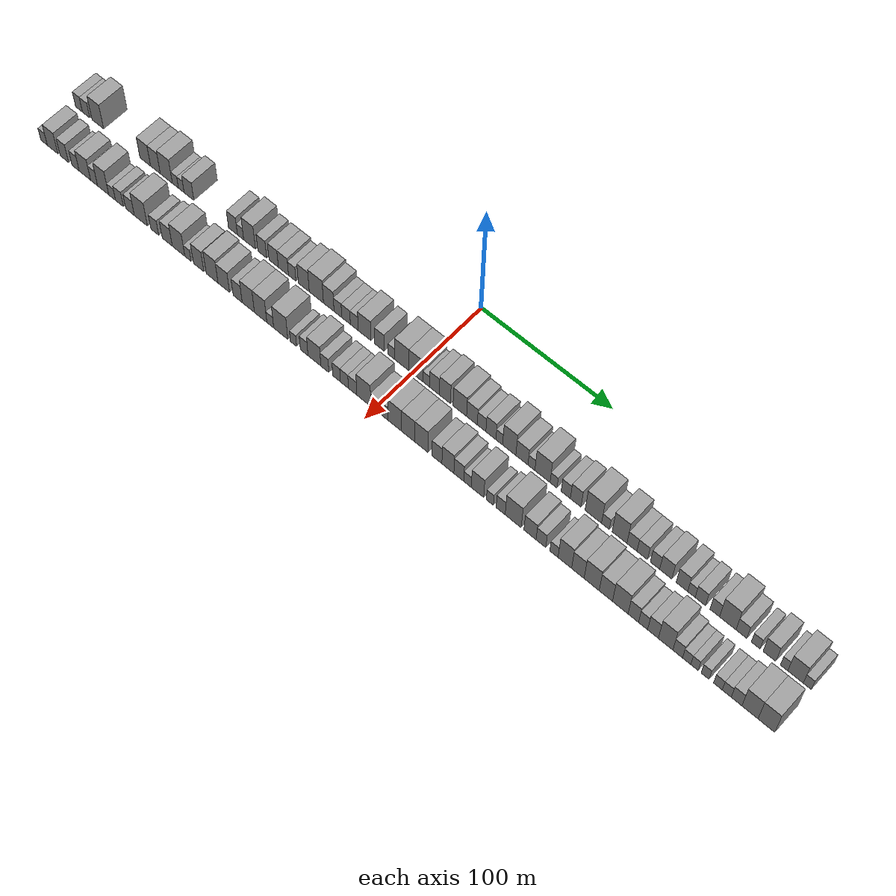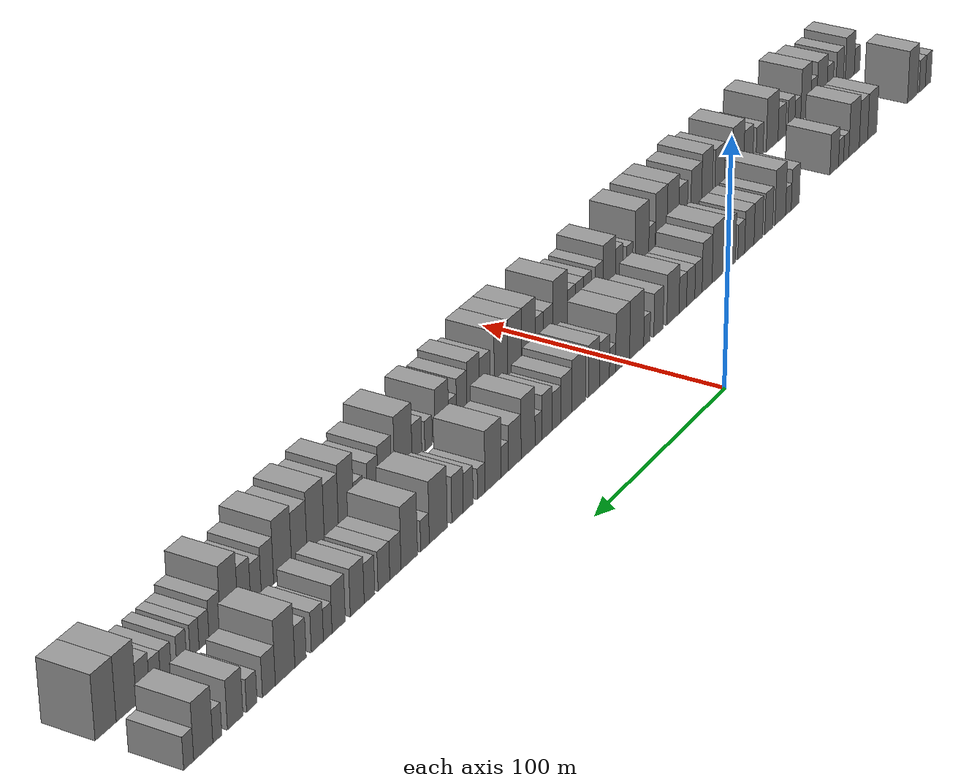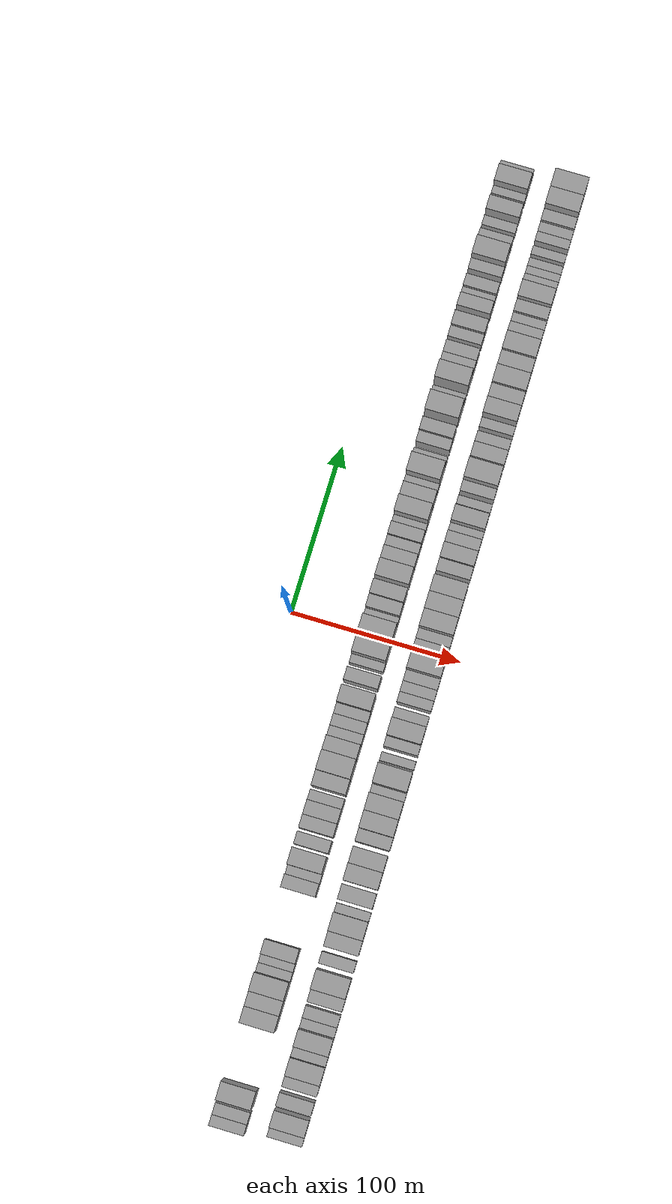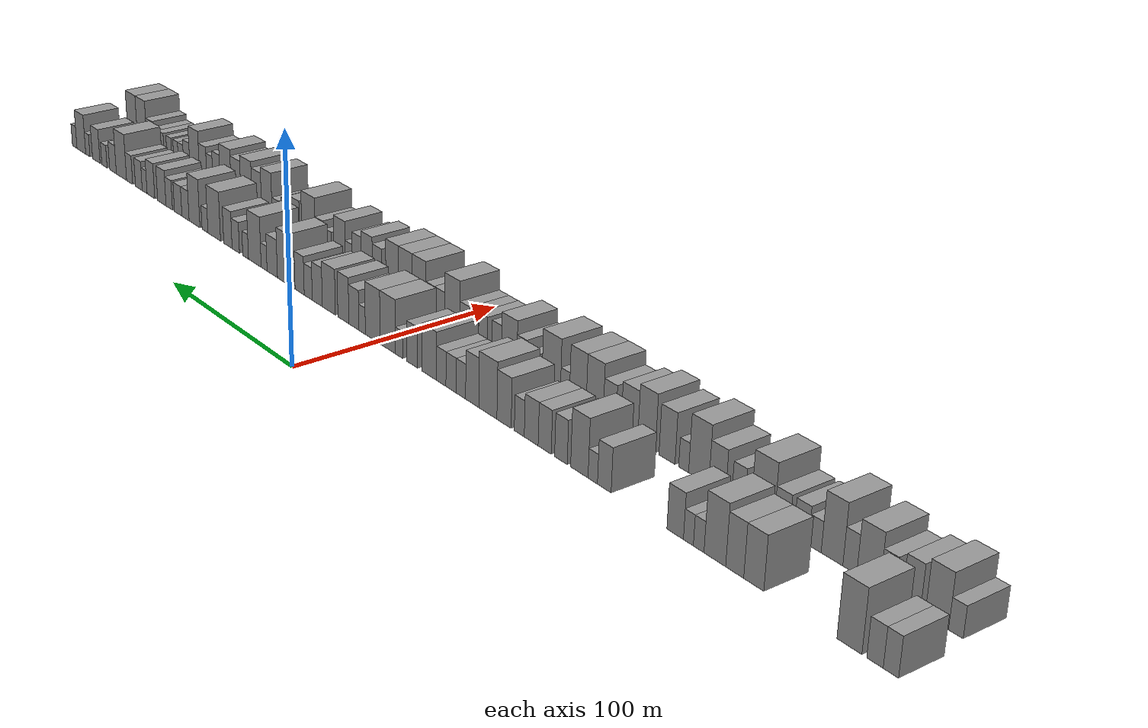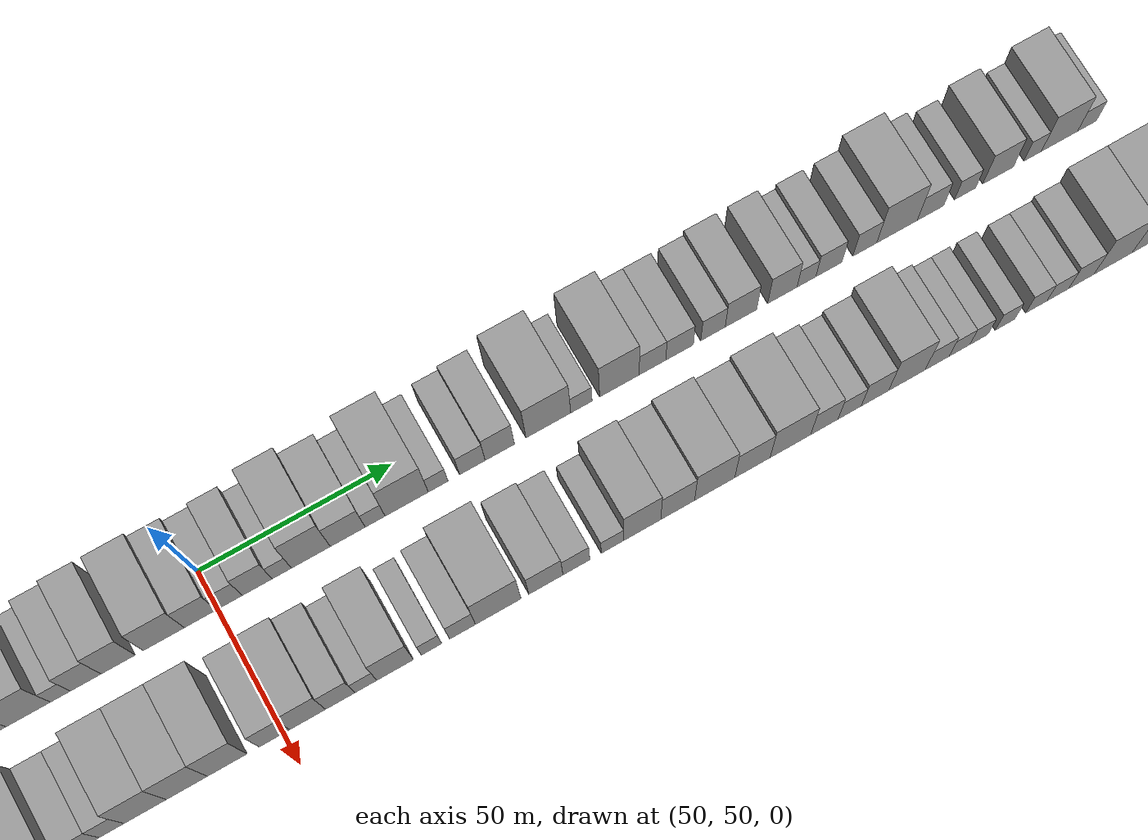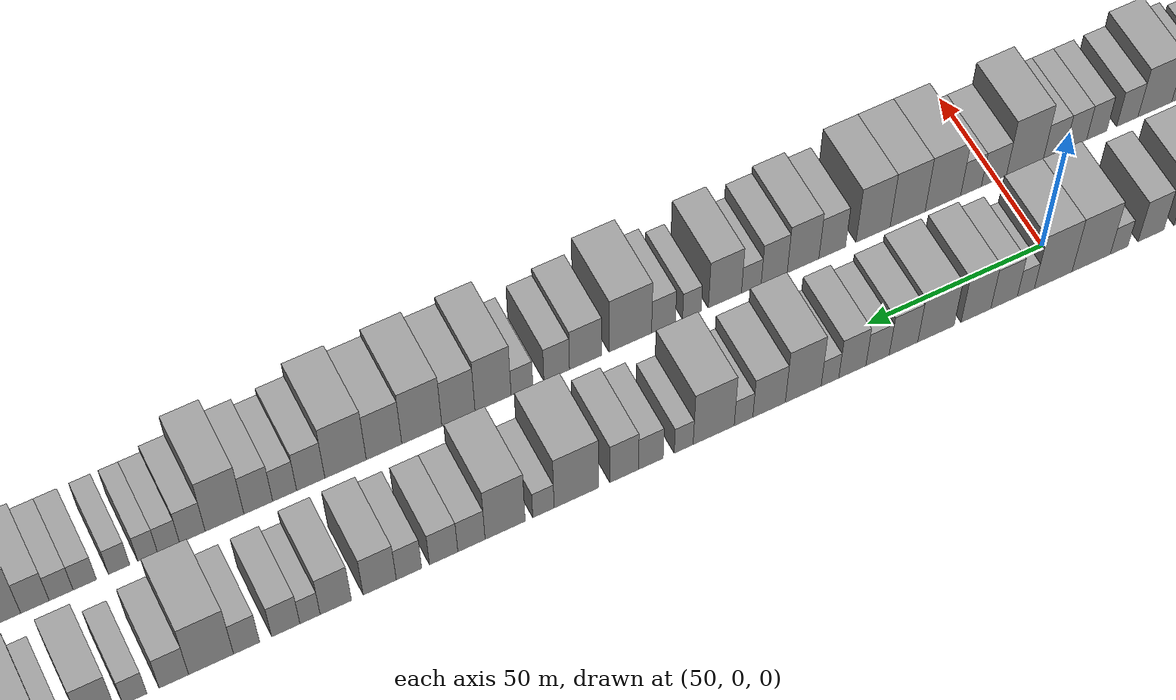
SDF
<sdf version="1.6">
 <world name="default">
  <scene>
   <sky><clouds><speed>12</speed></clouds></sky>
   <ambient>0.4 0.4 0.4 1</ambient>
   <background>0.7 0.7 0.7 1</background>
   <shadows>1</shadows>
  </scene>
  <gravity>0 0 -9.8066</gravity>
  <magnetic_field>6e-06 2.3e-05 -4.2e-05</magnetic_field>
  <physics default="0" name="default_physics" type="ode">
   <ode>
    <solver>
     <type>quick</type>
     <iters>10</iters>
     <sor>1.0</sor>
     <use_dynamic_moi_rescaling>0</use_dynamic_moi_rescaling>
    </solver>
    <constraints>
     <cfm>0</cfm>
     <erp>0.2</erp>
     <contact_max_correcting_vel>100</contact_max_correcting_vel>
     <contact_surface_layer>0.001</contact_surface_layer>
    </constraints>
   </ode>
   <max_step_size>0.004</max_step_size>
   <real_time_factor>1</real_time_factor>
   <real_time_update_rate>250</real_time_update_rate>
  </physics>
  <light name="sun" type="directional">
   <pose>0 0 10 0 0 0</pose>
   <diffuse>0.8 0.8 0.8 1</diffuse>
   <specular>0.2 0.2 0.2 1</specular>
   <attenuation>
    <range>1000</range>
    <constant>0.9</constant>
    <linear>0.01</linear>
    <quadratic>0.001</quadratic>
   </attenuation>
   <direction>-0.5 0.1 -0.9</direction>
  </light>
  <model name="building_1">
   <static>1</static>
   <pose>50.0000 -280.9047 0 0.000000 0.000000 0.000000</pose>
   <link name="link">
    <pose>0 0 7.50 0 0 0</pose>
    <collision name="collision"><geometry><box><size>20.0000 6.1906 15.0000</size></box></geometry></collision>
    <visual name="visual">
     <cast_shadows>0</cast_shadows>
     <geometry><box><size>20.0000 6.1906 15.0000</size></box></geometry>
     <material>
      <script>
       <uri>model://grey_wall/materials/scripts</uri>
       <uri>model://grey_wall/materials/textures</uri>
       <name>vrc/grey_wall</name>
      </script>
     </material>
    </visual>
   </link>
  </model>
  <model name="building_2">
   <static>1</static>
   <pose>50.0000 -274.4337 0 0.000000 0.000000 0.000000</pose>
   <link name="link">
    <pose>0 0 7.50 0 0 0</pose>
    <collision name="collision"><geometry><box><size>20.0000 6.7513 15.0000</size></box></geometry></collision>
    <visual name="visual">
     <cast_shadows>0</cast_shadows>
     <geometry><box><size>20.0000 6.7513 15.0000</size></box></geometry>
     <material>
      <script>
       <uri>model://grey_wall/materials/scripts</uri>
       <uri>model://grey_wall/materials/textures</uri>
       <name>vrc/grey_wall</name>
      </script>
     </material>
    </visual>
   </link>
  </model>
  <model name="building_3">
   <static>1</static>
   <pose>50.0000 -263.8113 0 0.000000 0.000000 0.000000</pose>
   <link name="link">
    <pose>0 0 12.00 0 0 0</pose>
    <collision name="collision"><geometry><box><size>20.0000 10.4937 24.0000</size></box></geometry></collision>
    <visual name="visual">
     <cast_shadows>0</cast_shadows>
     <geometry><box><size>20.0000 10.4937 24.0000</size></box></geometry>
     <material>
      <script>
       <uri>model://grey_wall/materials/scripts</uri>
       <uri>model://grey_wall/materials/textures</uri>
       <name>vrc/grey_wall</name>
      </script>
     </material>
    </visual>
   </link>
  </model>
  <model name="building_4">
   <static>1</static>
   <pose>50.0000 -221.5287 0 0.000000 0.000000 0.000000</pose>
   <link name="link">
    <pose>0 0 10.50 0 0 0</pose>
    <collision name="collision"><geometry><box><size>20.0000 9.3572 21.0000</size></box></geometry></collision>
    <visual name="visual">
     <cast_shadows>0</cast_shadows>
     <geometry><box><size>20.0000 9.3572 21.0000</size></box></geometry>
     <material>
      <script>
       <uri>model://grey_wall/materials/scripts</uri>
       <uri>model://grey_wall/materials/textures</uri>
       <name>vrc/grey_wall</name>
      </script>
     </material>
    </visual>
   </link>
  </model>
  <model name="building_5">
   <static>1</static>
   <pose>50.0000 -212.5647 0 0.000000 0.000000 0.000000</pose>
   <link name="link">
    <pose>0 0 10.50 0 0 0</pose>
    <collision name="collision"><geometry><box><size>20.0000 8.5709 21.0000</size></box></geometry></collision>
    <visual name="visual">
     <cast_shadows>0</cast_shadows>
     <geometry><box><size>20.0000 8.5709 21.0000</size></box></geometry>
     <material>
      <script>
       <uri>model://grey_wall/materials/scripts</uri>
       <uri>model://grey_wall/materials/textures</uri>
       <name>vrc/grey_wall</name>
      </script>
     </material>
    </visual>
   </link>
  </model>
  <model name="building_6">
   <static>1</static>
   <pose>50.0000 -203.0101 0 0.000000 0.000000 0.000000</pose>
   <link name="link">
    <pose>0 0 12.00 0 0 0</pose>
    <collision name="collision"><geometry><box><size>20.0000 10.5382 24.0000</size></box></geometry></collision>
    <visual name="visual">
     <cast_shadows>0</cast_shadows>
     <geometry><box><size>20.0000 10.5382 24.0000</size></box></geometry>
     <material>
      <script>
       <uri>model://grey_wall/materials/scripts</uri>
       <uri>model://grey_wall/materials/textures</uri>
       <name>vrc/grey_wall</name>
      </script>
     </material>
    </visual>
   </link>
  </model>
  <model name="building_7">
   <static>1</static>
   <pose>50.0000 -195.1155 0 0.000000 0.000000 0.000000</pose>
   <link name="link">
    <pose>0 0 6.00 0 0 0</pose>
    <collision name="collision"><geometry><box><size>20.0000 5.2510 12.0000</size></box></geometry></collision>
    <visual name="visual">
     <cast_shadows>0</cast_shadows>
     <geometry><box><size>20.0000 5.2510 12.0000</size></box></geometry>
     <material>
      <script>
       <uri>model://grey_wall/materials/scripts</uri>
       <uri>model://grey_wall/materials/textures</uri>
       <name>vrc/grey_wall</name>
      </script>
     </material>
    </visual>
   </link>
  </model>
  <model name="building_8">
   <static>1</static>
   <pose>50.0000 -190.0040 0 0.000000 0.000000 0.000000</pose>
   <link name="link">
    <pose>0 0 6.00 0 0 0</pose>
    <collision name="collision"><geometry><box><size>20.0000 4.9719 12.0000</size></box></geometry></collision>
    <visual name="visual">
     <cast_shadows>0</cast_shadows>
     <geometry><box><size>20.0000 4.9719 12.0000</size></box></geometry>
     <material>
      <script>
       <uri>model://grey_wall/materials/scripts</uri>
       <uri>model://grey_wall/materials/textures</uri>
       <name>vrc/grey_wall</name>
      </script>
     </material>
    </visual>
   </link>
  </model>
  <model name="building_9">
   <static>1</static>
   <pose>50.0000 -183.3172 0 0.000000 0.000000 0.000000</pose>
   <link name="link">
    <pose>0 0 9.00 0 0 0</pose>
    <collision name="collision"><geometry><box><size>20.0000 8.4017 18.0000</size></box></geometry></collision>
    <visual name="visual">
     <cast_shadows>0</cast_shadows>
     <geometry><box><size>20.0000 8.4017 18.0000</size></box></geometry>
     <material>
      <script>
       <uri>model://grey_wall/materials/scripts</uri>
       <uri>model://grey_wall/materials/textures</uri>
       <name>vrc/grey_wall</name>
      </script>
     </material>
    </visual>
   </link>
  </model>
  <model name="building_10">
   <static>1</static>
   <pose>50.0000 -145.7531 0 0.000000 0.000000 0.000000</pose>
   <link name="link">
    <pose>0 0 9.00 0 0 0</pose>
    <collision name="collision"><geometry><box><size>20.0000 7.5755 18.0000</size></box></geometry></collision>
    <visual name="visual">
     <cast_shadows>0</cast_shadows>
     <geometry><box><size>20.0000 7.5755 18.0000</size></box></geometry>
     <material>
      <script>
       <uri>model://grey_wall/materials/scripts</uri>
       <uri>model://grey_wall/materials/textures</uri>
       <name>vrc/grey_wall</name>
      </script>
     </material>
    </visual>
   </link>
  </model>
  <model name="building_11">
   <static>1</static>
   <pose>50.0000 -139.3310 0 0.000000 0.000000 0.000000</pose>
   <link name="link">
    <pose>0 0 6.00 0 0 0</pose>
    <collision name="collision"><geometry><box><size>20.0000 5.2685 12.0000</size></box></geometry></collision>
    <visual name="visual">
     <cast_shadows>0</cast_shadows>
     <geometry><box><size>20.0000 5.2685 12.0000</size></box></geometry>
     <material>
      <script>
       <uri>model://grey_wall/materials/scripts</uri>
       <uri>model://grey_wall/materials/textures</uri>
       <name>vrc/grey_wall</name>
      </script>
     </material>
    </visual>
   </link>
  </model>
  <model name="building_12">
   <static>1</static>
   <pose>50.0000 -131.7397 0 0.000000 0.000000 0.000000</pose>
   <link name="link">
    <pose>0 0 12.00 0 0 0</pose>
    <collision name="collision"><geometry><box><size>20.0000 9.9141 24.0000</size></box></geometry></collision>
    <visual name="visual">
     <cast_shadows>0</cast_shadows>
     <geometry><box><size>20.0000 9.9141 24.0000</size></box></geometry>
     <material>
      <script>
       <uri>model://grey_wall/materials/scripts</uri>
       <uri>model://grey_wall/materials/textures</uri>
       <name>vrc/grey_wall</name>
      </script>
     </material>
    </visual>
   </link>
  </model>
  <model name="building_13">
   <static>1</static>
   <pose>50.0000 -121.1283 0 0.000000 0.000000 0.000000</pose>
   <link name="link">
    <pose>0 0 9.00 0 0 0</pose>
    <collision name="collision"><geometry><box><size>20.0000 7.3088 18.0000</size></box></geometry></collision>
    <visual name="visual">
     <cast_shadows>0</cast_shadows>
     <geometry><box><size>20.0000 7.3088 18.0000</size></box></geometry>
     <material>
      <script>
       <uri>model://grey_wall/materials/scripts</uri>
       <uri>model://grey_wall/materials/textures</uri>
       <name>vrc/grey_wall</name>
      </script>
     </material>
    </visual>
   </link>
  </model>
  <model name="building_14">
   <static>1</static>
   <pose>50.0000 -111.5930 0 0.000000 0.000000 0.000000</pose>
   <link name="link">
    <pose>0 0 9.00 0 0 0</pose>
    <collision name="collision"><geometry><box><size>20.0000 7.7617 18.0000</size></box></geometry></collision>
    <visual name="visual">
     <cast_shadows>0</cast_shadows>
     <geometry><box><size>20.0000 7.7617 18.0000</size></box></geometry>
     <material>
      <script>
       <uri>model://grey_wall/materials/scripts</uri>
       <uri>model://grey_wall/materials/textures</uri>
       <name>vrc/grey_wall</name>
      </script>
     </material>
    </visual>
   </link>
  </model>
  <model name="building_15">
   <static>1</static>
   <pose>50.0000 -103.5192 0 0.000000 0.000000 0.000000</pose>
   <link name="link">
    <pose>0 0 9.00 0 0 0</pose>
    <collision name="collision"><geometry><box><size>20.0000 8.3860 18.0000</size></box></geometry></collision>
    <visual name="visual">
     <cast_shadows>0</cast_shadows>
     <geometry><box><size>20.0000 8.3860 18.0000</size></box></geometry>
     <material>
      <script>
       <uri>model://grey_wall/materials/scripts</uri>
       <uri>model://grey_wall/materials/textures</uri>
       <name>vrc/grey_wall</name>
      </script>
     </material>
    </visual>
   </link>
  </model>
  <model name="building_16">
   <static>1</static>
   <pose>50.0000 -96.2797 0 0.000000 0.000000 0.000000</pose>
   <link name="link">
    <pose>0 0 7.50 0 0 0</pose>
    <collision name="collision"><geometry><box><size>20.0000 6.0930 15.0000</size></box></geometry></collision>
    <visual name="visual">
     <cast_shadows>0</cast_shadows>
     <geometry><box><size>20.0000 6.0930 15.0000</size></box></geometry>
     <material>
      <script>
       <uri>model://grey_wall/materials/scripts</uri>
       <uri>model://grey_wall/materials/textures</uri>
       <name>vrc/grey_wall</name>
      </script>
     </material>
    </visual>
   </link>
  </model>
  <model name="building_17">
   <static>1</static>
   <pose>50.0000 -86.7857 0 0.000000 0.000000 0.000000</pose>
   <link name="link">
    <pose>0 0 10.50 0 0 0</pose>
    <collision name="collision"><geometry><box><size>20.0000 8.8949 21.0000</size></box></geometry></collision>
    <visual name="visual">
     <cast_shadows>0</cast_shadows>
     <geometry><box><size>20.0000 8.8949 21.0000</size></box></geometry>
     <material>
      <script>
       <uri>model://grey_wall/materials/scripts</uri>
       <uri>model://grey_wall/materials/textures</uri>
       <name>vrc/grey_wall</name>
      </script>
     </material>
    </visual>
   </link>
  </model>
  <model name="building_18">
   <static>1</static>
   <pose>50.0000 -76.5486 0 0.000000 0.000000 0.000000</pose>
   <link name="link">
    <pose>0 0 12.00 0 0 0</pose>
    <collision name="collision"><geometry><box><size>20.0000 11.5792 24.0000</size></box></geometry></collision>
    <visual name="visual">
     <cast_shadows>0</cast_shadows>
     <geometry><box><size>20.0000 11.5792 24.0000</size></box></geometry>
     <material>
      <script>
       <uri>model://grey_wall/materials/scripts</uri>
       <uri>model://grey_wall/materials/textures</uri>
       <name>vrc/grey_wall</name>
      </script>
     </material>
    </visual>
   </link>
  </model>
  <model name="building_19">
   <static>1</static>
   <pose>50.0000 -66.4720 0 0.000000 0.000000 0.000000</pose>
   <link name="link">
    <pose>0 0 10.50 0 0 0</pose>
    <collision name="collision"><geometry><box><size>20.0000 8.5740 21.0000</size></box></geometry></collision>
    <visual name="visual">
     <cast_shadows>0</cast_shadows>
     <geometry><box><size>20.0000 8.5740 21.0000</size></box></geometry>
     <material>
      <script>
       <uri>model://grey_wall/materials/scripts</uri>
       <uri>model://grey_wall/materials/textures</uri>
       <name>vrc/grey_wall</name>
      </script>
     </material>
    </visual>
   </link>
  </model>
  <model name="building_20">
   <static>1</static>
   <pose>50.0000 -59.0821 0 0.000000 0.000000 0.000000</pose>
   <link name="link">
    <pose>0 0 7.50 0 0 0</pose>
    <collision name="collision"><geometry><box><size>20.0000 6.2059 15.0000</size></box></geometry></collision>
    <visual name="visual">
     <cast_shadows>0</cast_shadows>
     <geometry><box><size>20.0000 6.2059 15.0000</size></box></geometry>
     <material>
      <script>
       <uri>model://grey_wall/materials/scripts</uri>
       <uri>model://grey_wall/materials/textures</uri>
       <name>vrc/grey_wall</name>
      </script>
     </material>
    </visual>
   </link>
  </model>
  <model name="building_21">
   <static>1</static>
   <pose>50.0000 -52.5241 0 0.000000 0.000000 0.000000</pose>
   <link name="link">
    <pose>0 0 7.50 0 0 0</pose>
    <collision name="collision"><geometry><box><size>20.0000 6.9101 15.0000</size></box></geometry></collision>
    <visual name="visual">
     <cast_shadows>0</cast_shadows>
     <geometry><box><size>20.0000 6.9101 15.0000</size></box></geometry>
     <material>
      <script>
       <uri>model://grey_wall/materials/scripts</uri>
       <uri>model://grey_wall/materials/textures</uri>
       <name>vrc/grey_wall</name>
      </script>
     </material>
    </visual>
   </link>
  </model>
  <model name="building_22">
   <static>1</static>
   <pose>50.0000 -45.9291 0 0.000000 0.000000 0.000000</pose>
   <link name="link">
    <pose>0 0 7.50 0 0 0</pose>
    <collision name="collision"><geometry><box><size>20.0000 6.2798 15.0000</size></box></geometry></collision>
    <visual name="visual">
     <cast_shadows>0</cast_shadows>
     <geometry><box><size>20.0000 6.2798 15.0000</size></box></geometry>
     <material>
      <script>
       <uri>model://grey_wall/materials/scripts</uri>
       <uri>model://grey_wall/materials/textures</uri>
       <name>vrc/grey_wall</name>
      </script>
     </material>
    </visual>
   </link>
  </model>
  <model name="building_23">
   <static>1</static>
   <pose>50.0000 -37.7250 0 0.000000 0.000000 0.000000</pose>
   <link name="link">
    <pose>0 0 10.50 0 0 0</pose>
    <collision name="collision"><geometry><box><size>20.0000 10.1284 21.0000</size></box></geometry></collision>
    <visual name="visual">
     <cast_shadows>0</cast_shadows>
     <geometry><box><size>20.0000 10.1284 21.0000</size></box></geometry>
     <material>
      <script>
       <uri>model://grey_wall/materials/scripts</uri>
       <uri>model://grey_wall/materials/textures</uri>
       <name>vrc/grey_wall</name>
      </script>
     </material>
    </visual>
   </link>
  </model>
  <model name="building_24">
   <static>1</static>
   <pose>50.0000 -25.8488 0 0.000000 0.000000 0.000000</pose>
   <link name="link">
    <pose>0 0 9.00 0 0 0</pose>
    <collision name="collision"><geometry><box><size>20.0000 7.6238 18.0000</size></box></geometry></collision>
    <visual name="visual">
     <cast_shadows>0</cast_shadows>
     <geometry><box><size>20.0000 7.6238 18.0000</size></box></geometry>
     <material>
      <script>
       <uri>model://grey_wall/materials/scripts</uri>
       <uri>model://grey_wall/materials/textures</uri>
       <name>vrc/grey_wall</name>
      </script>
     </material>
    </visual>
   </link>
  </model>
  <model name="building_25">
   <static>1</static>
   <pose>50.0000 -16.4413 0 0.000000 0.000000 0.000000</pose>
   <link name="link">
    <pose>0 0 6.00 0 0 0</pose>
    <collision name="collision"><geometry><box><size>20.0000 5.1911 12.0000</size></box></geometry></collision>
    <visual name="visual">
     <cast_shadows>0</cast_shadows>
     <geometry><box><size>20.0000 5.1911 12.0000</size></box></geometry>
     <material>
      <script>
       <uri>model://grey_wall/materials/scripts</uri>
       <uri>model://grey_wall/materials/textures</uri>
       <name>vrc/grey_wall</name>
      </script>
     </material>
    </visual>
   </link>
  </model>
  <model name="building_26">
   <static>1</static>
   <pose>50.0000 -8.2512 0 0.000000 0.000000 0.000000</pose>
   <link name="link">
    <pose>0 0 12.00 0 0 0</pose>
    <collision name="collision"><geometry><box><size>20.0000 11.1893 24.0000</size></box></geometry></collision>
    <visual name="visual">
     <cast_shadows>0</cast_shadows>
     <geometry><box><size>20.0000 11.1893 24.0000</size></box></geometry>
     <material>
      <script>
       <uri>model://grey_wall/materials/scripts</uri>
       <uri>model://grey_wall/materials/textures</uri>
       <name>vrc/grey_wall</name>
      </script>
     </material>
    </visual>
   </link>
  </model>
  <model name="building_27">
   <static>1</static>
   <pose>50.0000 2.8335 0 0.000000 0.000000 0.000000</pose>
   <link name="link">
    <pose>0 0 12.00 0 0 0</pose>
    <collision name="collision"><geometry><box><size>20.0000 10.9800 24.0000</size></box></geometry></collision>
    <visual name="visual">
     <cast_shadows>0</cast_shadows>
     <geometry><box><size>20.0000 10.9800 24.0000</size></box></geometry>
     <material>
      <script>
       <uri>model://grey_wall/materials/scripts</uri>
       <uri>model://grey_wall/materials/textures</uri>
       <name>vrc/grey_wall</name>
      </script>
     </material>
    </visual>
   </link>
  </model>
  <model name="building_28">
   <static>1</static>
   <pose>50.0000 10.7881 0 0.000000 0.000000 0.000000</pose>
   <link name="link">
    <pose>0 0 6.00 0 0 0</pose>
    <collision name="collision"><geometry><box><size>20.0000 4.9293 12.0000</size></box></geometry></collision>
    <visual name="visual">
     <cast_shadows>0</cast_shadows>
     <geometry><box><size>20.0000 4.9293 12.0000</size></box></geometry>
     <material>
      <script>
       <uri>model://grey_wall/materials/scripts</uri>
       <uri>model://grey_wall/materials/textures</uri>
       <name>vrc/grey_wall</name>
      </script>
     </material>
    </visual>
   </link>
  </model>
  <model name="building_29">
   <static>1</static>
   <pose>50.0000 17.0681 0 0.000000 0.000000 0.000000</pose>
   <link name="link">
    <pose>0 0 9.00 0 0 0</pose>
    <collision name="collision"><geometry><box><size>20.0000 7.6307 18.0000</size></box></geometry></collision>
    <visual name="visual">
     <cast_shadows>0</cast_shadows>
     <geometry><box><size>20.0000 7.6307 18.0000</size></box></geometry>
     <material>
      <script>
       <uri>model://grey_wall/materials/scripts</uri>
       <uri>model://grey_wall/materials/textures</uri>
       <name>vrc/grey_wall</name>
      </script>
     </material>
    </visual>
   </link>
  </model>
  <model name="building_30">
   <static>1</static>
   <pose>50.0000 25.1394 0 0.000000 0.000000 0.000000</pose>
   <link name="link">
    <pose>0 0 10.50 0 0 0</pose>
    <collision name="collision"><geometry><box><size>20.0000 8.5120 21.0000</size></box></geometry></collision>
    <visual name="visual">
     <cast_shadows>0</cast_shadows>
     <geometry><box><size>20.0000 8.5120 21.0000</size></box></geometry>
     <material>
      <script>
       <uri>model://grey_wall/materials/scripts</uri>
       <uri>model://grey_wall/materials/textures</uri>
       <name>vrc/grey_wall</name>
      </script>
     </material>
    </visual>
   </link>
  </model>
  <model name="building_31">
   <static>1</static>
   <pose>50.0000 36.5549 0 0.000000 0.000000 0.000000</pose>
   <link name="link">
    <pose>0 0 10.50 0 0 0</pose>
    <collision name="collision"><geometry><box><size>20.0000 10.3190 21.0000</size></box></geometry></collision>
    <visual name="visual">
     <cast_shadows>0</cast_shadows>
     <geometry><box><size>20.0000 10.3190 21.0000</size></box></geometry>
     <material>
      <script>
       <uri>model://grey_wall/materials/scripts</uri>
       <uri>model://grey_wall/materials/textures</uri>
       <name>vrc/grey_wall</name>
      </script>
     </material>
    </visual>
   </link>
  </model>
  <model name="building_32">
   <static>1</static>
   <pose>50.0000 45.7655 0 0.000000 0.000000 0.000000</pose>
   <link name="link">
    <pose>0 0 9.00 0 0 0</pose>
    <collision name="collision"><geometry><box><size>20.0000 8.1023 18.0000</size></box></geometry></collision>
    <visual name="visual">
     <cast_shadows>0</cast_shadows>
     <geometry><box><size>20.0000 8.1023 18.0000</size></box></geometry>
     <material>
      <script>
       <uri>model://grey_wall/materials/scripts</uri>
       <uri>model://grey_wall/materials/textures</uri>
       <name>vrc/grey_wall</name>
      </script>
     </material>
    </visual>
   </link>
  </model>
  <model name="building_33">
   <static>1</static>
   <pose>50.0000 53.0973 0 0.000000 0.000000 0.000000</pose>
   <link name="link">
    <pose>0 0 7.50 0 0 0</pose>
    <collision name="collision"><geometry><box><size>20.0000 6.5614 15.0000</size></box></geometry></collision>
    <visual name="visual">
     <cast_shadows>0</cast_shadows>
     <geometry><box><size>20.0000 6.5614 15.0000</size></box></geometry>
     <material>
      <script>
       <uri>model://grey_wall/materials/scripts</uri>
       <uri>model://grey_wall/materials/textures</uri>
       <name>vrc/grey_wall</name>
      </script>
     </material>
    </visual>
   </link>
  </model>
  <model name="building_34">
   <static>1</static>
   <pose>50.0000 60.1738 0 0.000000 0.000000 0.000000</pose>
   <link name="link">
    <pose>0 0 9.00 0 0 0</pose>
    <collision name="collision"><geometry><box><size>20.0000 7.5915 18.0000</size></box></geometry></collision>
    <visual name="visual">
     <cast_shadows>0</cast_shadows>
     <geometry><box><size>20.0000 7.5915 18.0000</size></box></geometry>
     <material>
      <script>
       <uri>model://grey_wall/materials/scripts</uri>
       <uri>model://grey_wall/materials/textures</uri>
       <name>vrc/grey_wall</name>
      </script>
     </material>
    </visual>
   </link>
  </model>
  <model name="building_35">
   <static>1</static>
   <pose>50.0000 66.4325 0 0.000000 0.000000 0.000000</pose>
   <link name="link">
    <pose>0 0 6.00 0 0 0</pose>
    <collision name="collision"><geometry><box><size>20.0000 4.9259 12.0000</size></box></geometry></collision>
    <visual name="visual">
     <cast_shadows>0</cast_shadows>
     <geometry><box><size>20.0000 4.9259 12.0000</size></box></geometry>
     <material>
      <script>
       <uri>model://grey_wall/materials/scripts</uri>
       <uri>model://grey_wall/materials/textures</uri>
       <name>vrc/grey_wall</name>
      </script>
     </material>
    </visual>
   </link>
  </model>
  <model name="building_36">
   <static>1</static>
   <pose>50.0000 73.8627 0 0.000000 0.000000 0.000000</pose>
   <link name="link">
    <pose>0 0 12.00 0 0 0</pose>
    <collision name="collision"><geometry><box><size>20.0000 9.9345 24.0000</size></box></geometry></collision>
    <visual name="visual">
     <cast_shadows>0</cast_shadows>
     <geometry><box><size>20.0000 9.9345 24.0000</size></box></geometry>
     <material>
      <script>
       <uri>model://grey_wall/materials/scripts</uri>
       <uri>model://grey_wall/materials/textures</uri>
       <name>vrc/grey_wall</name>
      </script>
     </material>
    </visual>
   </link>
  </model>
  <model name="building_37">
   <static>1</static>
   <pose>50.0000 83.3168 0 0.000000 0.000000 0.000000</pose>
   <link name="link">
    <pose>0 0 9.00 0 0 0</pose>
    <collision name="collision"><geometry><box><size>20.0000 8.9738 18.0000</size></box></geometry></collision>
    <visual name="visual">
     <cast_shadows>0</cast_shadows>
     <geometry><box><size>20.0000 8.9738 18.0000</size></box></geometry>
     <material>
      <script>
       <uri>model://grey_wall/materials/scripts</uri>
       <uri>model://grey_wall/materials/textures</uri>
       <name>vrc/grey_wall</name>
      </script>
     </material>
    </visual>
   </link>
  </model>
  <model name="building_38">
   <static>1</static>
   <pose>50.0000 90.3598 0 0.000000 0.000000 0.000000</pose>
   <link name="link">
    <pose>0 0 6.00 0 0 0</pose>
    <collision name="collision"><geometry><box><size>20.0000 5.1121 12.0000</size></box></geometry></collision>
    <visual name="visual">
     <cast_shadows>0</cast_shadows>
     <geometry><box><size>20.0000 5.1121 12.0000</size></box></geometry>
     <material>
      <script>
       <uri>model://grey_wall/materials/scripts</uri>
       <uri>model://grey_wall/materials/textures</uri>
       <name>vrc/grey_wall</name>
      </script>
     </material>
    </visual>
   </link>
  </model>
  <model name="building_39">
   <static>1</static>
   <pose>50.0000 98.5224 0 0.000000 0.000000 0.000000</pose>
   <link name="link">
    <pose>0 0 12.00 0 0 0</pose>
    <collision name="collision"><geometry><box><size>20.0000 11.2131 24.0000</size></box></geometry></collision>
    <visual name="visual">
     <cast_shadows>0</cast_shadows>
     <geometry><box><size>20.0000 11.2131 24.0000</size></box></geometry>
     <material>
      <script>
       <uri>model://grey_wall/materials/scripts</uri>
       <uri>model://grey_wall/materials/textures</uri>
       <name>vrc/grey_wall</name>
      </script>
     </material>
    </visual>
   </link>
  </model>
  <model name="building_40">
   <static>1</static>
   <pose>50.0000 106.6938 0 0.000000 0.000000 0.000000</pose>
   <link name="link">
    <pose>0 0 6.00 0 0 0</pose>
    <collision name="collision"><geometry><box><size>20.0000 5.1296 12.0000</size></box></geometry></collision>
    <visual name="visual">
     <cast_shadows>0</cast_shadows>
     <geometry><box><size>20.0000 5.1296 12.0000</size></box></geometry>
     <material>
      <script>
       <uri>model://grey_wall/materials/scripts</uri>
       <uri>model://grey_wall/materials/textures</uri>
       <name>vrc/grey_wall</name>
      </script>
     </material>
    </visual>
   </link>
  </model>
  <model name="building_41">
   <static>1</static>
   <pose>50.0000 115.6049 0 0.000000 0.000000 0.000000</pose>
   <link name="link">
    <pose>0 0 7.50 0 0 0</pose>
    <collision name="collision"><geometry><box><size>20.0000 6.6927 15.0000</size></box></geometry></collision>
    <visual name="visual">
     <cast_shadows>0</cast_shadows>
     <geometry><box><size>20.0000 6.6927 15.0000</size></box></geometry>
     <material>
      <script>
       <uri>model://grey_wall/materials/scripts</uri>
       <uri>model://grey_wall/materials/textures</uri>
       <name>vrc/grey_wall</name>
      </script>
     </material>
    </visual>
   </link>
  </model>
  <model name="building_42">
   <static>1</static>
   <pose>50.0000 122.7920 0 0.000000 0.000000 0.000000</pose>
   <link name="link">
    <pose>0 0 9.00 0 0 0</pose>
    <collision name="collision"><geometry><box><size>20.0000 7.6814 18.0000</size></box></geometry></collision>
    <visual name="visual">
     <cast_shadows>0</cast_shadows>
     <geometry><box><size>20.0000 7.6814 18.0000</size></box></geometry>
     <material>
      <script>
       <uri>model://grey_wall/materials/scripts</uri>
       <uri>model://grey_wall/materials/textures</uri>
       <name>vrc/grey_wall</name>
      </script>
     </material>
    </visual>
   </link>
  </model>
  <model name="building_43">
   <static>1</static>
   <pose>50.0000 135.5515 0 0.000000 0.000000 0.000000</pose>
   <link name="link">
    <pose>0 0 12.00 0 0 0</pose>
    <collision name="collision"><geometry><box><size>20.0000 11.8377 24.0000</size></box></geometry></collision>
    <visual name="visual">
     <cast_shadows>0</cast_shadows>
     <geometry><box><size>20.0000 11.8377 24.0000</size></box></geometry>
     <material>
      <script>
       <uri>model://grey_wall/materials/scripts</uri>
       <uri>model://grey_wall/materials/textures</uri>
       <name>vrc/grey_wall</name>
      </script>
     </material>
    </visual>
   </link>
  </model>
  <model name="building_44">
   <static>1</static>
   <pose>50.0000 144.2986 0 0.000000 0.000000 0.000000</pose>
   <link name="link">
    <pose>0 0 6.00 0 0 0</pose>
    <collision name="collision"><geometry><box><size>20.0000 5.6564 12.0000</size></box></geometry></collision>
    <visual name="visual">
     <cast_shadows>0</cast_shadows>
     <geometry><box><size>20.0000 5.6564 12.0000</size></box></geometry>
     <material>
      <script>
       <uri>model://grey_wall/materials/scripts</uri>
       <uri>model://grey_wall/materials/textures</uri>
       <name>vrc/grey_wall</name>
      </script>
     </material>
    </visual>
   </link>
  </model>
  <model name="building_45">
   <static>1</static>
   <pose>50.0000 154.3961 0 0.000000 0.000000 0.000000</pose>
   <link name="link">
    <pose>0 0 12.00 0 0 0</pose>
    <collision name="collision"><geometry><box><size>20.0000 10.5387 24.0000</size></box></geometry></collision>
    <visual name="visual">
     <cast_shadows>0</cast_shadows>
     <geometry><box><size>20.0000 10.5387 24.0000</size></box></geometry>
     <material>
      <script>
       <uri>model://grey_wall/materials/scripts</uri>
       <uri>model://grey_wall/materials/textures</uri>
       <name>vrc/grey_wall</name>
      </script>
     </material>
    </visual>
   </link>
  </model>
  <model name="building_46">
   <static>1</static>
   <pose>50.0000 163.2297 0 0.000000 0.000000 0.000000</pose>
   <link name="link">
    <pose>0 0 7.50 0 0 0</pose>
    <collision name="collision"><geometry><box><size>20.0000 7.1285 15.0000</size></box></geometry></collision>
    <visual name="visual">
     <cast_shadows>0</cast_shadows>
     <geometry><box><size>20.0000 7.1285 15.0000</size></box></geometry>
     <material>
      <script>
       <uri>model://grey_wall/materials/scripts</uri>
       <uri>model://grey_wall/materials/textures</uri>
       <name>vrc/grey_wall</name>
      </script>
     </material>
    </visual>
   </link>
  </model>
  <model name="building_47">
   <static>1</static>
   <pose>50.0000 170.4870 0 0.000000 0.000000 0.000000</pose>
   <link name="link">
    <pose>0 0 7.50 0 0 0</pose>
    <collision name="collision"><geometry><box><size>20.0000 7.3861 15.0000</size></box></geometry></collision>
    <visual name="visual">
     <cast_shadows>0</cast_shadows>
     <geometry><box><size>20.0000 7.3861 15.0000</size></box></geometry>
     <material>
      <script>
       <uri>model://grey_wall/materials/scripts</uri>
       <uri>model://grey_wall/materials/textures</uri>
       <name>vrc/grey_wall</name>
      </script>
     </material>
    </visual>
   </link>
  </model>
  <model name="building_48">
   <static>1</static>
   <pose>50.0000 179.4662 0 0.000000 0.000000 0.000000</pose>
   <link name="link">
    <pose>0 0 7.50 0 0 0</pose>
    <collision name="collision"><geometry><box><size>20.0000 6.5724 15.0000</size></box></geometry></collision>
    <visual name="visual">
     <cast_shadows>0</cast_shadows>
     <geometry><box><size>20.0000 6.5724 15.0000</size></box></geometry>
     <material>
      <script>
       <uri>model://grey_wall/materials/scripts</uri>
       <uri>model://grey_wall/materials/textures</uri>
       <name>vrc/grey_wall</name>
      </script>
     </material>
    </visual>
   </link>
  </model>
  <model name="building_49">
   <static>1</static>
   <pose>50.0000 187.0171 0 0.000000 0.000000 0.000000</pose>
   <link name="link">
    <pose>0 0 9.00 0 0 0</pose>
    <collision name="collision"><geometry><box><size>20.0000 8.5294 18.0000</size></box></geometry></collision>
    <visual name="visual">
     <cast_shadows>0</cast_shadows>
     <geometry><box><size>20.0000 8.5294 18.0000</size></box></geometry>
     <material>
      <script>
       <uri>model://grey_wall/materials/scripts</uri>
       <uri>model://grey_wall/materials/textures</uri>
       <name>vrc/grey_wall</name>
      </script>
     </material>
    </visual>
   </link>
  </model>
  <model name="building_50">
   <static>1</static>
   <pose>50.0000 198.2740 0 0.000000 0.000000 0.000000</pose>
   <link name="link">
    <pose>0 0 9.00 0 0 0</pose>
    <collision name="collision"><geometry><box><size>20.0000 7.9844 18.0000</size></box></geometry></collision>
    <visual name="visual">
     <cast_shadows>0</cast_shadows>
     <geometry><box><size>20.0000 7.9844 18.0000</size></box></geometry>
     <material>
      <script>
       <uri>model://grey_wall/materials/scripts</uri>
       <uri>model://grey_wall/materials/textures</uri>
       <name>vrc/grey_wall</name>
      </script>
     </material>
    </visual>
   </link>
  </model>
  <model name="building_51">
   <static>1</static>
   <pose>50.0000 204.8367 0 0.000000 0.000000 0.000000</pose>
   <link name="link">
    <pose>0 0 6.00 0 0 0</pose>
    <collision name="collision"><geometry><box><size>20.0000 5.1409 12.0000</size></box></geometry></collision>
    <visual name="visual">
     <cast_shadows>0</cast_shadows>
     <geometry><box><size>20.0000 5.1409 12.0000</size></box></geometry>
     <material>
      <script>
       <uri>model://grey_wall/materials/scripts</uri>
       <uri>model://grey_wall/materials/textures</uri>
       <name>vrc/grey_wall</name>
      </script>
     </material>
    </visual>
   </link>
  </model>
  <model name="building_52">
   <static>1</static>
   <pose>50.0000 210.9923 0 0.000000 0.000000 0.000000</pose>
   <link name="link">
    <pose>0 0 7.50 0 0 0</pose>
    <collision name="collision"><geometry><box><size>20.0000 7.1704 15.0000</size></box></geometry></collision>
    <visual name="visual">
     <cast_shadows>0</cast_shadows>
     <geometry><box><size>20.0000 7.1704 15.0000</size></box></geometry>
     <material>
      <script>
       <uri>model://grey_wall/materials/scripts</uri>
       <uri>model://grey_wall/materials/textures</uri>
       <name>vrc/grey_wall</name>
      </script>
     </material>
    </visual>
   </link>
  </model>
  <model name="building_53">
   <static>1</static>
   <pose>50.0000 220.8630 0 0.000000 0.000000 0.000000</pose>
   <link name="link">
    <pose>0 0 7.50 0 0 0</pose>
    <collision name="collision"><geometry><box><size>20.0000 6.5710 15.0000</size></box></geometry></collision>
    <visual name="visual">
     <cast_shadows>0</cast_shadows>
     <geometry><box><size>20.0000 6.5710 15.0000</size></box></geometry>
     <material>
      <script>
       <uri>model://grey_wall/materials/scripts</uri>
       <uri>model://grey_wall/materials/textures</uri>
       <name>vrc/grey_wall</name>
      </script>
     </material>
    </visual>
   </link>
  </model>
  <model name="building_54">
   <static>1</static>
   <pose>50.0000 229.7604 0 0.000000 0.000000 0.000000</pose>
   <link name="link">
    <pose>0 0 12.00 0 0 0</pose>
    <collision name="collision"><geometry><box><size>20.0000 11.2237 24.0000</size></box></geometry></collision>
    <visual name="visual">
     <cast_shadows>0</cast_shadows>
     <geometry><box><size>20.0000 11.2237 24.0000</size></box></geometry>
     <material>
      <script>
       <uri>model://grey_wall/materials/scripts</uri>
       <uri>model://grey_wall/materials/textures</uri>
       <name>vrc/grey_wall</name>
      </script>
     </material>
    </visual>
   </link>
  </model>
  <model name="building_55">
   <static>1</static>
   <pose>50.0000 239.0391 0 0.000000 0.000000 0.000000</pose>
   <link name="link">
    <pose>0 0 7.50 0 0 0</pose>
    <collision name="collision"><geometry><box><size>20.0000 7.3338 15.0000</size></box></geometry></collision>
    <visual name="visual">
     <cast_shadows>0</cast_shadows>
     <geometry><box><size>20.0000 7.3338 15.0000</size></box></geometry>
     <material>
      <script>
       <uri>model://grey_wall/materials/scripts</uri>
       <uri>model://grey_wall/materials/textures</uri>
       <name>vrc/grey_wall</name>
      </script>
     </material>
    </visual>
   </link>
  </model>
  <model name="building_56">
   <static>1</static>
   <pose>50.0000 248.6575 0 0.000000 0.000000 0.000000</pose>
   <link name="link">
    <pose>0 0 6.00 0 0 0</pose>
    <collision name="collision"><geometry><box><size>20.0000 5.9029 12.0000</size></box></geometry></collision>
    <visual name="visual">
     <cast_shadows>0</cast_shadows>
     <geometry><box><size>20.0000 5.9029 12.0000</size></box></geometry>
     <material>
      <script>
       <uri>model://grey_wall/materials/scripts</uri>
       <uri>model://grey_wall/materials/textures</uri>
       <name>vrc/grey_wall</name>
      </script>
     </material>
    </visual>
   </link>
  </model>
  <model name="building_57">
   <static>1</static>
   <pose>50.0000 257.8917 0 0.000000 0.000000 0.000000</pose>
   <link name="link">
    <pose>0 0 9.00 0 0 0</pose>
    <collision name="collision"><geometry><box><size>20.0000 8.5654 18.0000</size></box></geometry></collision>
    <visual name="visual">
     <cast_shadows>0</cast_shadows>
     <geometry><box><size>20.0000 8.5654 18.0000</size></box></geometry>
     <material>
      <script>
       <uri>model://grey_wall/materials/scripts</uri>
       <uri>model://grey_wall/materials/textures</uri>
       <name>vrc/grey_wall</name>
      </script>
     </material>
    </visual>
   </link>
  </model>
  <model name="building_58">
   <static>1</static>
   <pose>50.0000 267.6285 0 0.000000 0.000000 0.000000</pose>
   <link name="link">
    <pose>0 0 6.00 0 0 0</pose>
    <collision name="collision"><geometry><box><size>20.0000 4.9082 12.0000</size></box></geometry></collision>
    <visual name="visual">
     <cast_shadows>0</cast_shadows>
     <geometry><box><size>20.0000 4.9082 12.0000</size></box></geometry>
     <material>
      <script>
       <uri>model://grey_wall/materials/scripts</uri>
       <uri>model://grey_wall/materials/textures</uri>
       <name>vrc/grey_wall</name>
      </script>
     </material>
    </visual>
   </link>
  </model>
  <model name="building_59">
   <static>1</static>
   <pose>50.0000 275.2060 0 0.000000 0.000000 0.000000</pose>
   <link name="link">
    <pose>0 0 10.50 0 0 0</pose>
    <collision name="collision"><geometry><box><size>20.0000 10.2468 21.0000</size></box></geometry></collision>
    <visual name="visual">
     <cast_shadows>0</cast_shadows>
     <geometry><box><size>20.0000 10.2468 21.0000</size></box></geometry>
     <material>
      <script>
       <uri>model://grey_wall/materials/scripts</uri>
       <uri>model://grey_wall/materials/textures</uri>
       <name>vrc/grey_wall</name>
      </script>
     </material>
    </visual>
   </link>
  </model>
  <model name="building_60">
   <static>1</static>
   <pose>50.0000 283.0019 0 0.000000 0.000000 0.000000</pose>
   <link name="link">
    <pose>0 0 6.00 0 0 0</pose>
    <collision name="collision"><geometry><box><size>20.0000 5.3450 12.0000</size></box></geometry></collision>
    <visual name="visual">
     <cast_shadows>0</cast_shadows>
     <geometry><box><size>20.0000 5.3450 12.0000</size></box></geometry>
     <material>
      <script>
       <uri>model://grey_wall/materials/scripts</uri>
       <uri>model://grey_wall/materials/textures</uri>
       <name>vrc/grey_wall</name>
      </script>
     </material>
    </visual>
   </link>
  </model>
  <model name="building_61">
   <static>1</static>
   <pose>82.0000 -278.0445 0 0.000000 0.000000 0.000000</pose>
   <link name="link">
    <pose>0 0 6.00 0 0 0</pose>
    <collision name="collision"><geometry><box><size>20.0000 5.9109 12.0000</size></box></geometry></collision>
    <visual name="visual">
     <cast_shadows>0</cast_shadows>
     <geometry><box><size>20.0000 5.9109 12.0000</size></box></geometry>
     <material>
      <script>
       <uri>model://grey_wall/materials/scripts</uri>
       <uri>model://grey_wall/materials/textures</uri>
       <name>vrc/grey_wall</name>
      </script>
     </material>
    </visual>
   </link>
  </model>
  <model name="building_62">
   <static>1</static>
   <pose>82.0000 -270.2772 0 0.000000 0.000000 0.000000</pose>
   <link name="link">
    <pose>0 0 10.50 0 0 0</pose>
    <collision name="collision"><geometry><box><size>20.0000 9.6237 21.0000</size></box></geometry></collision>
    <visual name="visual">
     <cast_shadows>0</cast_shadows>
     <geometry><box><size>20.0000 9.6237 21.0000</size></box></geometry>
     <material>
      <script>
       <uri>model://grey_wall/materials/scripts</uri>
       <uri>model://grey_wall/materials/textures</uri>
       <name>vrc/grey_wall</name>
      </script>
     </material>
    </visual>
   </link>
  </model>
  <model name="building_63">
   <static>1</static>
   <pose>82.0000 -259.6411 0 0.000000 0.000000 0.000000</pose>
   <link name="link">
    <pose>0 0 9.00 0 0 0</pose>
    <collision name="collision"><geometry><box><size>20.0000 7.6485 18.0000</size></box></geometry></collision>
    <visual name="visual">
     <cast_shadows>0</cast_shadows>
     <geometry><box><size>20.0000 7.6485 18.0000</size></box></geometry>
     <material>
      <script>
       <uri>model://grey_wall/materials/scripts</uri>
       <uri>model://grey_wall/materials/textures</uri>
       <name>vrc/grey_wall</name>
      </script>
     </material>
    </visual>
   </link>
  </model>
  <model name="building_64">
   <static>1</static>
   <pose>82.0000 -249.5891 0 0.000000 0.000000 0.000000</pose>
   <link name="link">
    <pose>0 0 7.50 0 0 0</pose>
    <collision name="collision"><geometry><box><size>20.0000 6.4555 15.0000</size></box></geometry></collision>
    <visual name="visual">
     <cast_shadows>0</cast_shadows>
     <geometry><box><size>20.0000 6.4555 15.0000</size></box></geometry>
     <material>
      <script>
       <uri>model://grey_wall/materials/scripts</uri>
       <uri>model://grey_wall/materials/textures</uri>
       <name>vrc/grey_wall</name>
      </script>
     </material>
    </visual>
   </link>
  </model>
  <model name="building_65">
   <static>1</static>
   <pose>82.0000 -241.2557 0 0.000000 0.000000 0.000000</pose>
   <link name="link">
    <pose>0 0 10.50 0 0 0</pose>
    <collision name="collision"><geometry><box><size>20.0000 10.2112 21.0000</size></box></geometry></collision>
    <visual name="visual">
     <cast_shadows>0</cast_shadows>
     <geometry><box><size>20.0000 10.2112 21.0000</size></box></geometry>
     <material>
      <script>
       <uri>model://grey_wall/materials/scripts</uri>
       <uri>model://grey_wall/materials/textures</uri>
       <name>vrc/grey_wall</name>
      </script>
     </material>
    </visual>
   </link>
  </model>
  <model name="building_66">
   <static>1</static>
   <pose>82.0000 -233.0473 0 0.000000 0.000000 0.000000</pose>
   <link name="link">
    <pose>0 0 7.50 0 0 0</pose>
    <collision name="collision"><geometry><box><size>20.0000 6.2056 15.0000</size></box></geometry></collision>
    <visual name="visual">
     <cast_shadows>0</cast_shadows>
     <geometry><box><size>20.0000 6.2056 15.0000</size></box></geometry>
     <material>
      <script>
       <uri>model://grey_wall/materials/scripts</uri>
       <uri>model://grey_wall/materials/textures</uri>
       <name>vrc/grey_wall</name>
      </script>
     </material>
    </visual>
   </link>
  </model>
  <model name="building_67">
   <static>1</static>
   <pose>82.0000 -225.0000 0 0.000000 0.000000 0.000000</pose>
   <link name="link">
    <pose>0 0 12.00 0 0 0</pose>
    <collision name="collision"><geometry><box><size>20.0000 9.8891 24.0000</size></box></geometry></collision>
    <visual name="visual">
     <cast_shadows>0</cast_shadows>
     <geometry><box><size>20.0000 9.8891 24.0000</size></box></geometry>
     <material>
      <script>
       <uri>model://grey_wall/materials/scripts</uri>
       <uri>model://grey_wall/materials/textures</uri>
       <name>vrc/grey_wall</name>
      </script>
     </material>
    </visual>
   </link>
  </model>
  <model name="building_68">
   <static>1</static>
   <pose>82.0000 -217.1194 0 0.000000 0.000000 0.000000</pose>
   <link name="link">
    <pose>0 0 6.00 0 0 0</pose>
    <collision name="collision"><geometry><box><size>20.0000 5.8720 12.0000</size></box></geometry></collision>
    <visual name="visual">
     <cast_shadows>0</cast_shadows>
     <geometry><box><size>20.0000 5.8720 12.0000</size></box></geometry>
     <material>
      <script>
       <uri>model://grey_wall/materials/scripts</uri>
       <uri>model://grey_wall/materials/textures</uri>
       <name>vrc/grey_wall</name>
      </script>
     </material>
    </visual>
   </link>
  </model>
  <model name="building_69">
   <static>1</static>
   <pose>82.0000 -210.7004 0 0.000000 0.000000 0.000000</pose>
   <link name="link">
    <pose>0 0 7.50 0 0 0</pose>
    <collision name="collision"><geometry><box><size>20.0000 6.9660 15.0000</size></box></geometry></collision>
    <visual name="visual">
     <cast_shadows>0</cast_shadows>
     <geometry><box><size>20.0000 6.9660 15.0000</size></box></geometry>
     <material>
      <script>
       <uri>model://grey_wall/materials/scripts</uri>
       <uri>model://grey_wall/materials/textures</uri>
       <name>vrc/grey_wall</name>
      </script>
     </material>
    </visual>
   </link>
  </model>
  <model name="building_70">
   <static>1</static>
   <pose>82.0000 -201.4727 0 0.000000 0.000000 0.000000</pose>
   <link name="link">
    <pose>0 0 7.50 0 0 0</pose>
    <collision name="collision"><geometry><box><size>20.0000 7.4895 15.0000</size></box></geometry></collision>
    <visual name="visual">
     <cast_shadows>0</cast_shadows>
     <geometry><box><size>20.0000 7.4895 15.0000</size></box></geometry>
     <material>
      <script>
       <uri>model://grey_wall/materials/scripts</uri>
       <uri>model://grey_wall/materials/textures</uri>
       <name>vrc/grey_wall</name>
      </script>
     </material>
    </visual>
   </link>
  </model>
  <model name="building_71">
   <static>1</static>
   <pose>82.0000 -192.0567 0 0.000000 0.000000 0.000000</pose>
   <link name="link">
    <pose>0 0 12.00 0 0 0</pose>
    <collision name="collision"><geometry><box><size>20.0000 11.3423 24.0000</size></box></geometry></collision>
    <visual name="visual">
     <cast_shadows>0</cast_shadows>
     <geometry><box><size>20.0000 11.3423 24.0000</size></box></geometry>
     <material>
      <script>
       <uri>model://grey_wall/materials/scripts</uri>
       <uri>model://grey_wall/materials/textures</uri>
       <name>vrc/grey_wall</name>
      </script>
     </material>
    </visual>
   </link>
  </model>
  <model name="building_72">
   <static>1</static>
   <pose>82.0000 -180.0124 0 0.000000 0.000000 0.000000</pose>
   <link name="link">
    <pose>0 0 7.50 0 0 0</pose>
    <collision name="collision"><geometry><box><size>20.0000 6.7464 15.0000</size></box></geometry></collision>
    <visual name="visual">
     <cast_shadows>0</cast_shadows>
     <geometry><box><size>20.0000 6.7464 15.0000</size></box></geometry>
     <material>
      <script>
       <uri>model://grey_wall/materials/scripts</uri>
       <uri>model://grey_wall/materials/textures</uri>
       <name>vrc/grey_wall</name>
      </script>
     </material>
    </visual>
   </link>
  </model>
  <model name="building_73">
   <static>1</static>
   <pose>82.0000 -169.2916 0 0.000000 0.000000 0.000000</pose>
   <link name="link">
    <pose>0 0 9.00 0 0 0</pose>
    <collision name="collision"><geometry><box><size>20.0000 8.6951 18.0000</size></box></geometry></collision>
    <visual name="visual">
     <cast_shadows>0</cast_shadows>
     <geometry><box><size>20.0000 8.6951 18.0000</size></box></geometry>
     <material>
      <script>
       <uri>model://grey_wall/materials/scripts</uri>
       <uri>model://grey_wall/materials/textures</uri>
       <name>vrc/grey_wall</name>
      </script>
     </material>
    </visual>
   </link>
  </model>
  <model name="building_74">
   <static>1</static>
   <pose>82.0000 -159.6134 0 0.000000 0.000000 0.000000</pose>
   <link name="link">
    <pose>0 0 12.00 0 0 0</pose>
    <collision name="collision"><geometry><box><size>20.0000 10.6612 24.0000</size></box></geometry></collision>
    <visual name="visual">
     <cast_shadows>0</cast_shadows>
     <geometry><box><size>20.0000 10.6612 24.0000</size></box></geometry>
     <material>
      <script>
       <uri>model://grey_wall/materials/scripts</uri>
       <uri>model://grey_wall/materials/textures</uri>
       <name>vrc/grey_wall</name>
      </script>
     </material>
    </visual>
   </link>
  </model>
  <model name="building_75">
   <static>1</static>
   <pose>82.0000 -151.6181 0 0.000000 0.000000 0.000000</pose>
   <link name="link">
    <pose>0 0 6.00 0 0 0</pose>
    <collision name="collision"><geometry><box><size>20.0000 5.3294 12.0000</size></box></geometry></collision>
    <visual name="visual">
     <cast_shadows>0</cast_shadows>
     <geometry><box><size>20.0000 5.3294 12.0000</size></box></geometry>
     <material>
      <script>
       <uri>model://grey_wall/materials/scripts</uri>
       <uri>model://grey_wall/materials/textures</uri>
       <name>vrc/grey_wall</name>
      </script>
     </material>
    </visual>
   </link>
  </model>
  <model name="building_76">
   <static>1</static>
   <pose>82.0000 -142.5731 0 0.000000 0.000000 0.000000</pose>
   <link name="link">
    <pose>0 0 10.50 0 0 0</pose>
    <collision name="collision"><geometry><box><size>20.0000 8.7606 21.0000</size></box></geometry></collision>
    <visual name="visual">
     <cast_shadows>0</cast_shadows>
     <geometry><box><size>20.0000 8.7606 21.0000</size></box></geometry>
     <material>
      <script>
       <uri>model://grey_wall/materials/scripts</uri>
       <uri>model://grey_wall/materials/textures</uri>
       <name>vrc/grey_wall</name>
      </script>
     </material>
    </visual>
   </link>
  </model>
  <model name="building_77">
   <static>1</static>
   <pose>82.0000 -131.2455 0 0.000000 0.000000 0.000000</pose>
   <link name="link">
    <pose>0 0 12.00 0 0 0</pose>
    <collision name="collision"><geometry><box><size>20.0000 9.8945 24.0000</size></box></geometry></collision>
    <visual name="visual">
     <cast_shadows>0</cast_shadows>
     <geometry><box><size>20.0000 9.8945 24.0000</size></box></geometry>
     <material>
      <script>
       <uri>model://grey_wall/materials/scripts</uri>
       <uri>model://grey_wall/materials/textures</uri>
       <name>vrc/grey_wall</name>
      </script>
     </material>
    </visual>
   </link>
  </model>
  <model name="building_78">
   <static>1</static>
   <pose>82.0000 -121.5096 0 0.000000 0.000000 0.000000</pose>
   <link name="link">
    <pose>0 0 10.50 0 0 0</pose>
    <collision name="collision"><geometry><box><size>20.0000 9.5774 21.0000</size></box></geometry></collision>
    <visual name="visual">
     <cast_shadows>0</cast_shadows>
     <geometry><box><size>20.0000 9.5774 21.0000</size></box></geometry>
     <material>
      <script>
       <uri>model://grey_wall/materials/scripts</uri>
       <uri>model://grey_wall/materials/textures</uri>
       <name>vrc/grey_wall</name>
      </script>
     </material>
    </visual>
   </link>
  </model>
  <model name="building_79">
   <static>1</static>
   <pose>82.0000 -109.9732 0 0.000000 0.000000 0.000000</pose>
   <link name="link">
    <pose>0 0 9.00 0 0 0</pose>
    <collision name="collision"><geometry><box><size>20.0000 7.4953 18.0000</size></box></geometry></collision>
    <visual name="visual">
     <cast_shadows>0</cast_shadows>
     <geometry><box><size>20.0000 7.4953 18.0000</size></box></geometry>
     <material>
      <script>
       <uri>model://grey_wall/materials/scripts</uri>
       <uri>model://grey_wall/materials/textures</uri>
       <name>vrc/grey_wall</name>
      </script>
     </material>
    </visual>
   </link>
  </model>
  <model name="building_80">
   <static>1</static>
   <pose>82.0000 -101.1580 0 0.000000 0.000000 0.000000</pose>
   <link name="link">
    <pose>0 0 12.00 0 0 0</pose>
    <collision name="collision"><geometry><box><size>20.0000 10.1350 24.0000</size></box></geometry></collision>
    <visual name="visual">
     <cast_shadows>0</cast_shadows>
     <geometry><box><size>20.0000 10.1350 24.0000</size></box></geometry>
     <material>
      <script>
       <uri>model://grey_wall/materials/scripts</uri>
       <uri>model://grey_wall/materials/textures</uri>
       <name>vrc/grey_wall</name>
      </script>
     </material>
    </visual>
   </link>
  </model>
  <model name="building_81">
   <static>1</static>
   <pose>82.0000 -91.0268 0 0.000000 0.000000 0.000000</pose>
   <link name="link">
    <pose>0 0 12.00 0 0 0</pose>
    <collision name="collision"><geometry><box><size>20.0000 10.1274 24.0000</size></box></geometry></collision>
    <visual name="visual">
     <cast_shadows>0</cast_shadows>
     <geometry><box><size>20.0000 10.1274 24.0000</size></box></geometry>
     <material>
      <script>
       <uri>model://grey_wall/materials/scripts</uri>
       <uri>model://grey_wall/materials/textures</uri>
       <name>vrc/grey_wall</name>
      </script>
     </material>
    </visual>
   </link>
  </model>
  <model name="building_82">
   <static>1</static>
   <pose>82.0000 -83.1672 0 0.000000 0.000000 0.000000</pose>
   <link name="link">
    <pose>0 0 6.00 0 0 0</pose>
    <collision name="collision"><geometry><box><size>20.0000 5.5919 12.0000</size></box></geometry></collision>
    <visual name="visual">
     <cast_shadows>0</cast_shadows>
     <geometry><box><size>20.0000 5.5919 12.0000</size></box></geometry>
     <material>
      <script>
       <uri>model://grey_wall/materials/scripts</uri>
       <uri>model://grey_wall/materials/textures</uri>
       <name>vrc/grey_wall</name>
      </script>
     </material>
    </visual>
   </link>
  </model>
  <model name="building_83">
   <static>1</static>
   <pose>82.0000 -74.6072 0 0.000000 0.000000 0.000000</pose>
   <link name="link">
    <pose>0 0 12.00 0 0 0</pose>
    <collision name="collision"><geometry><box><size>20.0000 11.5281 24.0000</size></box></geometry></collision>
    <visual name="visual">
     <cast_shadows>0</cast_shadows>
     <geometry><box><size>20.0000 11.5281 24.0000</size></box></geometry>
     <material>
      <script>
       <uri>model://grey_wall/materials/scripts</uri>
       <uri>model://grey_wall/materials/textures</uri>
       <name>vrc/grey_wall</name>
      </script>
     </material>
    </visual>
   </link>
  </model>
  <model name="building_84">
   <static>1</static>
   <pose>82.0000 -64.3022 0 0.000000 0.000000 0.000000</pose>
   <link name="link">
    <pose>0 0 6.00 0 0 0</pose>
    <collision name="collision"><geometry><box><size>20.0000 5.0819 12.0000</size></box></geometry></collision>
    <visual name="visual">
     <cast_shadows>0</cast_shadows>
     <geometry><box><size>20.0000 5.0819 12.0000</size></box></geometry>
     <material>
      <script>
       <uri>model://grey_wall/materials/scripts</uri>
       <uri>model://grey_wall/materials/textures</uri>
       <name>vrc/grey_wall</name>
      </script>
     </material>
    </visual>
   </link>
  </model>
  <model name="building_85">
   <static>1</static>
   <pose>82.0000 -55.6899 0 0.000000 0.000000 0.000000</pose>
   <link name="link">
    <pose>0 0 7.50 0 0 0</pose>
    <collision name="collision"><geometry><box><size>20.0000 6.1427 15.0000</size></box></geometry></collision>
    <visual name="visual">
     <cast_shadows>0</cast_shadows>
     <geometry><box><size>20.0000 6.1427 15.0000</size></box></geometry>
     <material>
      <script>
       <uri>model://grey_wall/materials/scripts</uri>
       <uri>model://grey_wall/materials/textures</uri>
       <name>vrc/grey_wall</name>
      </script>
     </material>
    </visual>
   </link>
  </model>
  <model name="building_86">
   <static>1</static>
   <pose>82.0000 -47.4825 0 0.000000 0.000000 0.000000</pose>
   <link name="link">
    <pose>0 0 10.50 0 0 0</pose>
    <collision name="collision"><geometry><box><size>20.0000 10.2721 21.0000</size></box></geometry></collision>
    <visual name="visual">
     <cast_shadows>0</cast_shadows>
     <geometry><box><size>20.0000 10.2721 21.0000</size></box></geometry>
     <material>
      <script>
       <uri>model://grey_wall/materials/scripts</uri>
       <uri>model://grey_wall/materials/textures</uri>
       <name>vrc/grey_wall</name>
      </script>
     </material>
    </visual>
   </link>
  </model>
  <model name="building_87">
   <static>1</static>
   <pose>82.0000 -39.1265 0 0.000000 0.000000 0.000000</pose>
   <link name="link">
    <pose>0 0 7.50 0 0 0</pose>
    <collision name="collision"><geometry><box><size>20.0000 6.4400 15.0000</size></box></geometry></collision>
    <visual name="visual">
     <cast_shadows>0</cast_shadows>
     <geometry><box><size>20.0000 6.4400 15.0000</size></box></geometry>
     <material>
      <script>
       <uri>model://grey_wall/materials/scripts</uri>
       <uri>model://grey_wall/materials/textures</uri>
       <name>vrc/grey_wall</name>
      </script>
     </material>
    </visual>
   </link>
  </model>
  <model name="building_88">
   <static>1</static>
   <pose>82.0000 -29.8760 0 0.000000 0.000000 0.000000</pose>
   <link name="link">
    <pose>0 0 7.50 0 0 0</pose>
    <collision name="collision"><geometry><box><size>20.0000 6.0609 15.0000</size></box></geometry></collision>
    <visual name="visual">
     <cast_shadows>0</cast_shadows>
     <geometry><box><size>20.0000 6.0609 15.0000</size></box></geometry>
     <material>
      <script>
       <uri>model://grey_wall/materials/scripts</uri>
       <uri>model://grey_wall/materials/textures</uri>
       <name>vrc/grey_wall</name>
      </script>
     </material>
    </visual>
   </link>
  </model>
  <model name="building_89">
   <static>1</static>
   <pose>82.0000 -23.6777 0 0.000000 0.000000 0.000000</pose>
   <link name="link">
    <pose>0 0 7.50 0 0 0</pose>
    <collision name="collision"><geometry><box><size>20.0000 6.3357 15.0000</size></box></geometry></collision>
    <visual name="visual">
     <cast_shadows>0</cast_shadows>
     <geometry><box><size>20.0000 6.3357 15.0000</size></box></geometry>
     <material>
      <script>
       <uri>model://grey_wall/materials/scripts</uri>
       <uri>model://grey_wall/materials/textures</uri>
       <name>vrc/grey_wall</name>
      </script>
     </material>
    </visual>
   </link>
  </model>
  <model name="building_90">
   <static>1</static>
   <pose>82.0000 -17.2185 0 0.000000 0.000000 0.000000</pose>
   <link name="link">
    <pose>0 0 7.50 0 0 0</pose>
    <collision name="collision"><geometry><box><size>20.0000 6.5828 15.0000</size></box></geometry></collision>
    <visual name="visual">
     <cast_shadows>0</cast_shadows>
     <geometry><box><size>20.0000 6.5828 15.0000</size></box></geometry>
     <material>
      <script>
       <uri>model://grey_wall/materials/scripts</uri>
       <uri>model://grey_wall/materials/textures</uri>
       <name>vrc/grey_wall</name>
      </script>
     </material>
    </visual>
   </link>
  </model>
  <model name="building_91">
   <static>1</static>
   <pose>82.0000 -8.4304 0 0.000000 0.000000 0.000000</pose>
   <link name="link">
    <pose>0 0 12.00 0 0 0</pose>
    <collision name="collision"><geometry><box><size>20.0000 10.9935 24.0000</size></box></geometry></collision>
    <visual name="visual">
     <cast_shadows>0</cast_shadows>
     <geometry><box><size>20.0000 10.9935 24.0000</size></box></geometry>
     <material>
      <script>
       <uri>model://grey_wall/materials/scripts</uri>
       <uri>model://grey_wall/materials/textures</uri>
       <name>vrc/grey_wall</name>
      </script>
     </material>
    </visual>
   </link>
  </model>
  <model name="building_92">
   <static>1</static>
   <pose>82.0000 0.7786 0 0.000000 0.000000 0.000000</pose>
   <link name="link">
    <pose>0 0 7.50 0 0 0</pose>
    <collision name="collision"><geometry><box><size>20.0000 7.4244 15.0000</size></box></geometry></collision>
    <visual name="visual">
     <cast_shadows>0</cast_shadows>
     <geometry><box><size>20.0000 7.4244 15.0000</size></box></geometry>
     <material>
      <script>
       <uri>model://grey_wall/materials/scripts</uri>
       <uri>model://grey_wall/materials/textures</uri>
       <name>vrc/grey_wall</name>
      </script>
     </material>
    </visual>
   </link>
  </model>
  <model name="building_93">
   <static>1</static>
   <pose>82.0000 7.5368 0 0.000000 0.000000 0.000000</pose>
   <link name="link">
    <pose>0 0 7.50 0 0 0</pose>
    <collision name="collision"><geometry><box><size>20.0000 6.0920 15.0000</size></box></geometry></collision>
    <visual name="visual">
     <cast_shadows>0</cast_shadows>
     <geometry><box><size>20.0000 6.0920 15.0000</size></box></geometry>
     <material>
      <script>
       <uri>model://grey_wall/materials/scripts</uri>
       <uri>model://grey_wall/materials/textures</uri>
       <name>vrc/grey_wall</name>
      </script>
     </material>
    </visual>
   </link>
  </model>
  <model name="building_94">
   <static>1</static>
   <pose>82.0000 15.7696 0 0.000000 0.000000 0.000000</pose>
   <link name="link">
    <pose>0 0 12.00 0 0 0</pose>
    <collision name="collision"><geometry><box><size>20.0000 10.3735 24.0000</size></box></geometry></collision>
    <visual name="visual">
     <cast_shadows>0</cast_shadows>
     <geometry><box><size>20.0000 10.3735 24.0000</size></box></geometry>
     <material>
      <script>
       <uri>model://grey_wall/materials/scripts</uri>
       <uri>model://grey_wall/materials/textures</uri>
       <name>vrc/grey_wall</name>
      </script>
     </material>
    </visual>
   </link>
  </model>
  <model name="building_95">
   <static>1</static>
   <pose>82.0000 26.0425 0 0.000000 0.000000 0.000000</pose>
   <link name="link">
    <pose>0 0 12.00 0 0 0</pose>
    <collision name="collision"><geometry><box><size>20.0000 10.1723 24.0000</size></box></geometry></collision>
    <visual name="visual">
     <cast_shadows>0</cast_shadows>
     <geometry><box><size>20.0000 10.1723 24.0000</size></box></geometry>
     <material>
      <script>
       <uri>model://grey_wall/materials/scripts</uri>
       <uri>model://grey_wall/materials/textures</uri>
       <name>vrc/grey_wall</name>
      </script>
     </material>
    </visual>
   </link>
  </model>
  <model name="building_96">
   <static>1</static>
   <pose>82.0000 36.0552 0 0.000000 0.000000 0.000000</pose>
   <link name="link">
    <pose>0 0 12.00 0 0 0</pose>
    <collision name="collision"><geometry><box><size>20.0000 9.8532 24.0000</size></box></geometry></collision>
    <visual name="visual">
     <cast_shadows>0</cast_shadows>
     <geometry><box><size>20.0000 9.8532 24.0000</size></box></geometry>
     <material>
      <script>
       <uri>model://grey_wall/materials/scripts</uri>
       <uri>model://grey_wall/materials/textures</uri>
       <name>vrc/grey_wall</name>
      </script>
     </material>
    </visual>
   </link>
  </model>
  <model name="building_97">
   <static>1</static>
   <pose>82.0000 47.7984 0 0.000000 0.000000 0.000000</pose>
   <link name="link">
    <pose>0 0 9.00 0 0 0</pose>
    <collision name="collision"><geometry><box><size>20.0000 7.6333 18.0000</size></box></geometry></collision>
    <visual name="visual">
     <cast_shadows>0</cast_shadows>
     <geometry><box><size>20.0000 7.6333 18.0000</size></box></geometry>
     <material>
      <script>
       <uri>model://grey_wall/materials/scripts</uri>
       <uri>model://grey_wall/materials/textures</uri>
       <name>vrc/grey_wall</name>
      </script>
     </material>
    </visual>
   </link>
  </model>
  <model name="building_98">
   <static>1</static>
   <pose>82.0000 56.1274 0 0.000000 0.000000 0.000000</pose>
   <link name="link">
    <pose>0 0 10.50 0 0 0</pose>
    <collision name="collision"><geometry><box><size>20.0000 9.0246 21.0000</size></box></geometry></collision>
    <visual name="visual">
     <cast_shadows>0</cast_shadows>
     <geometry><box><size>20.0000 9.0246 21.0000</size></box></geometry>
     <material>
      <script>
       <uri>model://grey_wall/materials/scripts</uri>
       <uri>model://grey_wall/materials/textures</uri>
       <name>vrc/grey_wall</name>
      </script>
     </material>
    </visual>
   </link>
  </model>
  <model name="building_99">
   <static>1</static>
   <pose>82.0000 64.3355 0 0.000000 0.000000 0.000000</pose>
   <link name="link">
    <pose>0 0 9.00 0 0 0</pose>
    <collision name="collision"><geometry><box><size>20.0000 7.3915 18.0000</size></box></geometry></collision>
    <visual name="visual">
     <cast_shadows>0</cast_shadows>
     <geometry><box><size>20.0000 7.3915 18.0000</size></box></geometry>
     <material>
      <script>
       <uri>model://grey_wall/materials/scripts</uri>
       <uri>model://grey_wall/materials/textures</uri>
       <name>vrc/grey_wall</name>
      </script>
     </material>
    </visual>
   </link>
  </model>
  <model name="building_100">
   <static>1</static>
   <pose>82.0000 70.8138 0 0.000000 0.000000 0.000000</pose>
   <link name="link">
    <pose>0 0 6.00 0 0 0</pose>
    <collision name="collision"><geometry><box><size>20.0000 5.5652 12.0000</size></box></geometry></collision>
    <visual name="visual">
     <cast_shadows>0</cast_shadows>
     <geometry><box><size>20.0000 5.5652 12.0000</size></box></geometry>
     <material>
      <script>
       <uri>model://grey_wall/materials/scripts</uri>
       <uri>model://grey_wall/materials/textures</uri>
       <name>vrc/grey_wall</name>
      </script>
     </material>
    </visual>
   </link>
  </model>
  <model name="building_101">
   <static>1</static>
   <pose>82.0000 78.2459 0 0.000000 0.000000 0.000000</pose>
   <link name="link">
    <pose>0 0 10.50 0 0 0</pose>
    <collision name="collision"><geometry><box><size>20.0000 9.2988 21.0000</size></box></geometry></collision>
    <visual name="visual">
     <cast_shadows>0</cast_shadows>
     <geometry><box><size>20.0000 9.2988 21.0000</size></box></geometry>
     <material>
      <script>
       <uri>model://grey_wall/materials/scripts</uri>
       <uri>model://grey_wall/materials/textures</uri>
       <name>vrc/grey_wall</name>
      </script>
     </material>
    </visual>
   </link>
  </model>
  <model name="building_102">
   <static>1</static>
   <pose>82.0000 87.4954 0 0.000000 0.000000 0.000000</pose>
   <link name="link">
    <pose>0 0 6.00 0 0 0</pose>
    <collision name="collision"><geometry><box><size>20.0000 5.2003 12.0000</size></box></geometry></collision>
    <visual name="visual">
     <cast_shadows>0</cast_shadows>
     <geometry><box><size>20.0000 5.2003 12.0000</size></box></geometry>
     <material>
      <script>
       <uri>model://grey_wall/materials/scripts</uri>
       <uri>model://grey_wall/materials/textures</uri>
       <name>vrc/grey_wall</name>
      </script>
     </material>
    </visual>
   </link>
  </model>
  <model name="building_103">
   <static>1</static>
   <pose>82.0000 95.4069 0 0.000000 0.000000 0.000000</pose>
   <link name="link">
    <pose>0 0 7.50 0 0 0</pose>
    <collision name="collision"><geometry><box><size>20.0000 6.6226 15.0000</size></box></geometry></collision>
    <visual name="visual">
     <cast_shadows>0</cast_shadows>
     <geometry><box><size>20.0000 6.6226 15.0000</size></box></geometry>
     <material>
      <script>
       <uri>model://grey_wall/materials/scripts</uri>
       <uri>model://grey_wall/materials/textures</uri>
       <name>vrc/grey_wall</name>
      </script>
     </material>
    </visual>
   </link>
  </model>
  <model name="building_104">
   <static>1</static>
   <pose>82.0000 104.5830 0 0.000000 0.000000 0.000000</pose>
   <link name="link">
    <pose>0 0 12.00 0 0 0</pose>
    <collision name="collision"><geometry><box><size>20.0000 11.7295 24.0000</size></box></geometry></collision>
    <visual name="visual">
     <cast_shadows>0</cast_shadows>
     <geometry><box><size>20.0000 11.7295 24.0000</size></box></geometry>
     <material>
      <script>
       <uri>model://grey_wall/materials/scripts</uri>
       <uri>model://grey_wall/materials/textures</uri>
       <name>vrc/grey_wall</name>
      </script>
     </material>
    </visual>
   </link>
  </model>
  <model name="building_105">
   <static>1</static>
   <pose>82.0000 116.8687 0 0.000000 0.000000 0.000000</pose>
   <link name="link">
    <pose>0 0 9.00 0 0 0</pose>
    <collision name="collision"><geometry><box><size>20.0000 8.8420 18.0000</size></box></geometry></collision>
    <visual name="visual">
     <cast_shadows>0</cast_shadows>
     <geometry><box><size>20.0000 8.8420 18.0000</size></box></geometry>
     <material>
      <script>
       <uri>model://grey_wall/materials/scripts</uri>
       <uri>model://grey_wall/materials/textures</uri>
       <name>vrc/grey_wall</name>
      </script>
     </material>
    </visual>
   </link>
  </model>
  <model name="building_106">
   <static>1</static>
   <pose>82.0000 124.7787 0 0.000000 0.000000 0.000000</pose>
   <link name="link">
    <pose>0 0 7.50 0 0 0</pose>
    <collision name="collision"><geometry><box><size>20.0000 6.9780 15.0000</size></box></geometry></collision>
    <visual name="visual">
     <cast_shadows>0</cast_shadows>
     <geometry><box><size>20.0000 6.9780 15.0000</size></box></geometry>
     <material>
      <script>
       <uri>model://grey_wall/materials/scripts</uri>
       <uri>model://grey_wall/materials/textures</uri>
       <name>vrc/grey_wall</name>
      </script>
     </material>
    </visual>
   </link>
  </model>
  <model name="building_107">
   <static>1</static>
   <pose>82.0000 134.2025 0 0.000000 0.000000 0.000000</pose>
   <link name="link">
    <pose>0 0 6.00 0 0 0</pose>
    <collision name="collision"><geometry><box><size>20.0000 5.8696 12.0000</size></box></geometry></collision>
    <visual name="visual">
     <cast_shadows>0</cast_shadows>
     <geometry><box><size>20.0000 5.8696 12.0000</size></box></geometry>
     <material>
      <script>
       <uri>model://grey_wall/materials/scripts</uri>
       <uri>model://grey_wall/materials/textures</uri>
       <name>vrc/grey_wall</name>
      </script>
     </material>
    </visual>
   </link>
  </model>
  <model name="building_108">
   <static>1</static>
   <pose>82.0000 141.9947 0 0.000000 0.000000 0.000000</pose>
   <link name="link">
    <pose>0 0 12.00 0 0 0</pose>
    <collision name="collision"><geometry><box><size>20.0000 9.7147 24.0000</size></box></geometry></collision>
    <visual name="visual">
     <cast_shadows>0</cast_shadows>
     <geometry><box><size>20.0000 9.7147 24.0000</size></box></geometry>
     <material>
      <script>
       <uri>model://grey_wall/materials/scripts</uri>
       <uri>model://grey_wall/materials/textures</uri>
       <name>vrc/grey_wall</name>
      </script>
     </material>
    </visual>
   </link>
  </model>
  <model name="building_109">
   <static>1</static>
   <pose>82.0000 151.2953 0 0.000000 0.000000 0.000000</pose>
   <link name="link">
    <pose>0 0 10.50 0 0 0</pose>
    <collision name="collision"><geometry><box><size>20.0000 8.8866 21.0000</size></box></geometry></collision>
    <visual name="visual">
     <cast_shadows>0</cast_shadows>
     <geometry><box><size>20.0000 8.8866 21.0000</size></box></geometry>
     <material>
      <script>
       <uri>model://grey_wall/materials/scripts</uri>
       <uri>model://grey_wall/materials/textures</uri>
       <name>vrc/grey_wall</name>
      </script>
     </material>
    </visual>
   </link>
  </model>
  <model name="building_110">
   <static>1</static>
   <pose>82.0000 161.0641 0 0.000000 0.000000 0.000000</pose>
   <link name="link">
    <pose>0 0 12.00 0 0 0</pose>
    <collision name="collision"><geometry><box><size>20.0000 10.6511 24.0000</size></box></geometry></collision>
    <visual name="visual">
     <cast_shadows>0</cast_shadows>
     <geometry><box><size>20.0000 10.6511 24.0000</size></box></geometry>
     <material>
      <script>
       <uri>model://grey_wall/materials/scripts</uri>
       <uri>model://grey_wall/materials/textures</uri>
       <name>vrc/grey_wall</name>
      </script>
     </material>
    </visual>
   </link>
  </model>
  <model name="building_111">
   <static>1</static>
   <pose>82.0000 171.0851 0 0.000000 0.000000 0.000000</pose>
   <link name="link">
    <pose>0 0 10.50 0 0 0</pose>
    <collision name="collision"><geometry><box><size>20.0000 9.3908 21.0000</size></box></geometry></collision>
    <visual name="visual">
     <cast_shadows>0</cast_shadows>
     <geometry><box><size>20.0000 9.3908 21.0000</size></box></geometry>
     <material>
      <script>
       <uri>model://grey_wall/materials/scripts</uri>
       <uri>model://grey_wall/materials/textures</uri>
       <name>vrc/grey_wall</name>
      </script>
     </material>
    </visual>
   </link>
  </model>
  <model name="building_112">
   <static>1</static>
   <pose>82.0000 181.2173 0 0.000000 0.000000 0.000000</pose>
   <link name="link">
    <pose>0 0 12.00 0 0 0</pose>
    <collision name="collision"><geometry><box><size>20.0000 10.8736 24.0000</size></box></geometry></collision>
    <visual name="visual">
     <cast_shadows>0</cast_shadows>
     <geometry><box><size>20.0000 10.8736 24.0000</size></box></geometry>
     <material>
      <script>
       <uri>model://grey_wall/materials/scripts</uri>
       <uri>model://grey_wall/materials/textures</uri>
       <name>vrc/grey_wall</name>
      </script>
     </material>
    </visual>
   </link>
  </model>
  <model name="building_113">
   <static>1</static>
   <pose>82.0000 190.3349 0 0.000000 0.000000 0.000000</pose>
   <link name="link">
    <pose>0 0 9.00 0 0 0</pose>
    <collision name="collision"><geometry><box><size>20.0000 7.3616 18.0000</size></box></geometry></collision>
    <visual name="visual">
     <cast_shadows>0</cast_shadows>
     <geometry><box><size>20.0000 7.3616 18.0000</size></box></geometry>
     <material>
      <script>
       <uri>model://grey_wall/materials/scripts</uri>
       <uri>model://grey_wall/materials/textures</uri>
       <name>vrc/grey_wall</name>
      </script>
     </material>
    </visual>
   </link>
  </model>
  <model name="building_114">
   <static>1</static>
   <pose>82.0000 197.1260 0 0.000000 0.000000 0.000000</pose>
   <link name="link">
    <pose>0 0 7.50 0 0 0</pose>
    <collision name="collision"><geometry><box><size>20.0000 6.2206 15.0000</size></box></geometry></collision>
    <visual name="visual">
     <cast_shadows>0</cast_shadows>
     <geometry><box><size>20.0000 6.2206 15.0000</size></box></geometry>
     <material>
      <script>
       <uri>model://grey_wall/materials/scripts</uri>
       <uri>model://grey_wall/materials/textures</uri>
       <name>vrc/grey_wall</name>
      </script>
     </material>
    </visual>
   </link>
  </model>
  <model name="building_115">
   <static>1</static>
   <pose>82.0000 203.9470 0 0.000000 0.000000 0.000000</pose>
   <link name="link">
    <pose>0 0 9.00 0 0 0</pose>
    <collision name="collision"><geometry><box><size>20.0000 7.4213 18.0000</size></box></geometry></collision>
    <visual name="visual">
     <cast_shadows>0</cast_shadows>
     <geometry><box><size>20.0000 7.4213 18.0000</size></box></geometry>
     <material>
      <script>
       <uri>model://grey_wall/materials/scripts</uri>
       <uri>model://grey_wall/materials/textures</uri>
       <name>vrc/grey_wall</name>
      </script>
     </material>
    </visual>
   </link>
  </model>
  <model name="building_116">
   <static>1</static>
   <pose>82.0000 212.6417 0 0.000000 0.000000 0.000000</pose>
   <link name="link">
    <pose>0 0 12.00 0 0 0</pose>
    <collision name="collision"><geometry><box><size>20.0000 9.9682 24.0000</size></box></geometry></collision>
    <visual name="visual">
     <cast_shadows>0</cast_shadows>
     <geometry><box><size>20.0000 9.9682 24.0000</size></box></geometry>
     <material>
      <script>
       <uri>model://grey_wall/materials/scripts</uri>
       <uri>model://grey_wall/materials/textures</uri>
       <name>vrc/grey_wall</name>
      </script>
     </material>
    </visual>
   </link>
  </model>
  <model name="building_117">
   <static>1</static>
   <pose>82.0000 220.9106 0 0.000000 0.000000 0.000000</pose>
   <link name="link">
    <pose>0 0 7.50 0 0 0</pose>
    <collision name="collision"><geometry><box><size>20.0000 6.5695 15.0000</size></box></geometry></collision>
    <visual name="visual">
     <cast_shadows>0</cast_shadows>
     <geometry><box><size>20.0000 6.5695 15.0000</size></box></geometry>
     <material>
      <script>
       <uri>model://grey_wall/materials/scripts</uri>
       <uri>model://grey_wall/materials/textures</uri>
       <name>vrc/grey_wall</name>
      </script>
     </material>
    </visual>
   </link>
  </model>
  <model name="building_118">
   <static>1</static>
   <pose>82.0000 227.0085 0 0.000000 0.000000 0.000000</pose>
   <link name="link">
    <pose>0 0 6.00 0 0 0</pose>
    <collision name="collision"><geometry><box><size>20.0000 5.6265 12.0000</size></box></geometry></collision>
    <visual name="visual">
     <cast_shadows>0</cast_shadows>
     <geometry><box><size>20.0000 5.6265 12.0000</size></box></geometry>
     <material>
      <script>
       <uri>model://grey_wall/materials/scripts</uri>
       <uri>model://grey_wall/materials/textures</uri>
       <name>vrc/grey_wall</name>
      </script>
     </material>
    </visual>
   </link>
  </model>
  <model name="building_119">
   <static>1</static>
   <pose>82.0000 232.3192 0 0.000000 0.000000 0.000000</pose>
   <link name="link">
    <pose>0 0 6.00 0 0 0</pose>
    <collision name="collision"><geometry><box><size>20.0000 4.9948 12.0000</size></box></geometry></collision>
    <visual name="visual">
     <cast_shadows>0</cast_shadows>
     <geometry><box><size>20.0000 4.9948 12.0000</size></box></geometry>
     <material>
      <script>
       <uri>model://grey_wall/materials/scripts</uri>
       <uri>model://grey_wall/materials/textures</uri>
       <name>vrc/grey_wall</name>
      </script>
     </material>
    </visual>
   </link>
  </model>
  <model name="building_120">
   <static>1</static>
   <pose>82.0000 239.5135 0 0.000000 0.000000 0.000000</pose>
   <link name="link">
    <pose>0 0 6.00 0 0 0</pose>
    <collision name="collision"><geometry><box><size>20.0000 5.3939 12.0000</size></box></geometry></collision>
    <visual name="visual">
     <cast_shadows>0</cast_shadows>
     <geometry><box><size>20.0000 5.3939 12.0000</size></box></geometry>
     <material>
      <script>
       <uri>model://grey_wall/materials/scripts</uri>
       <uri>model://grey_wall/materials/textures</uri>
       <name>vrc/grey_wall</name>
      </script>
     </material>
    </visual>
   </link>
  </model>
  <model name="building_121">
   <static>1</static>
   <pose>82.0000 248.1467 0 0.000000 0.000000 0.000000</pose>
   <link name="link">
    <pose>0 0 6.00 0 0 0</pose>
    <collision name="collision"><geometry><box><size>20.0000 5.8724 12.0000</size></box></geometry></collision>
    <visual name="visual">
     <cast_shadows>0</cast_shadows>
     <geometry><box><size>20.0000 5.8724 12.0000</size></box></geometry>
     <material>
      <script>
       <uri>model://grey_wall/materials/scripts</uri>
       <uri>model://grey_wall/materials/textures</uri>
       <name>vrc/grey_wall</name>
      </script>
     </material>
    </visual>
   </link>
  </model>
  <model name="building_122">
   <static>1</static>
   <pose>82.0000 254.0675 0 0.000000 0.000000 0.000000</pose>
   <link name="link">
    <pose>0 0 6.00 0 0 0</pose>
    <collision name="collision"><geometry><box><size>20.0000 5.9691 12.0000</size></box></geometry></collision>
    <visual name="visual">
     <cast_shadows>0</cast_shadows>
     <geometry><box><size>20.0000 5.9691 12.0000</size></box></geometry>
     <material>
      <script>
       <uri>model://grey_wall/materials/scripts</uri>
       <uri>model://grey_wall/materials/textures</uri>
       <name>vrc/grey_wall</name>
      </script>
     </material>
    </visual>
   </link>
  </model>
  <model name="building_123">
   <static>1</static>
   <pose>82.0000 260.5983 0 0.000000 0.000000 0.000000</pose>
   <link name="link">
    <pose>0 0 7.50 0 0 0</pose>
    <collision name="collision"><geometry><box><size>20.0000 7.0926 15.0000</size></box></geometry></collision>
    <visual name="visual">
     <cast_shadows>0</cast_shadows>
     <geometry><box><size>20.0000 7.0926 15.0000</size></box></geometry>
     <material>
      <script>
       <uri>model://grey_wall/materials/scripts</uri>
       <uri>model://grey_wall/materials/textures</uri>
       <name>vrc/grey_wall</name>
      </script>
     </material>
    </visual>
   </link>
  </model>
  <model name="building_124">
   <static>1</static>
   <pose>82.0000 269.4895 0 0.000000 0.000000 0.000000</pose>
   <link name="link">
    <pose>0 0 12.00 0 0 0</pose>
    <collision name="collision"><geometry><box><size>20.0000 10.6897 24.0000</size></box></geometry></collision>
    <visual name="visual">
     <cast_shadows>0</cast_shadows>
     <geometry><box><size>20.0000 10.6897 24.0000</size></box></geometry>
     <material>
      <script>
       <uri>model://grey_wall/materials/scripts</uri>
       <uri>model://grey_wall/materials/textures</uri>
       <name>vrc/grey_wall</name>
      </script>
     </material>
    </visual>
   </link>
  </model>
  <model name="building_125">
   <static>1</static>
   <pose>82.0000 280.3538 0 0.000000 0.000000 0.000000</pose>
   <link name="link">
    <pose>0 0 12.00 0 0 0</pose>
    <collision name="collision"><geometry><box><size>20.0000 11.0390 24.0000</size></box></geometry></collision>
    <visual name="visual">
     <cast_shadows>0</cast_shadows>
     <geometry><box><size>20.0000 11.0390 24.0000</size></box></geometry>
     <material>
      <script>
       <uri>model://grey_wall/materials/scripts</uri>
       <uri>model://grey_wall/materials/textures</uri>
       <name>vrc/grey_wall</name>
      </script>
     </material>
    </visual>
   </link>
  </model>
 </world>
</sdf>
